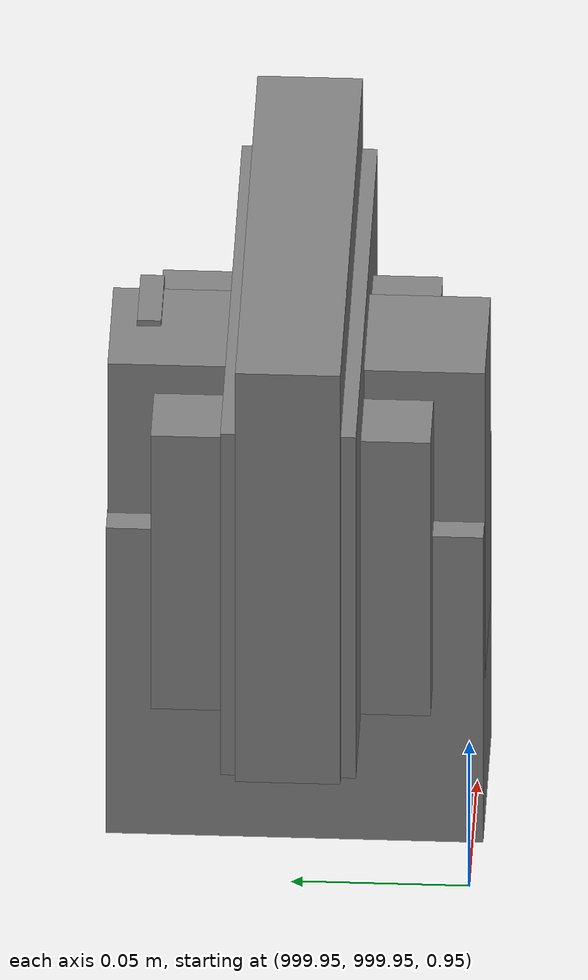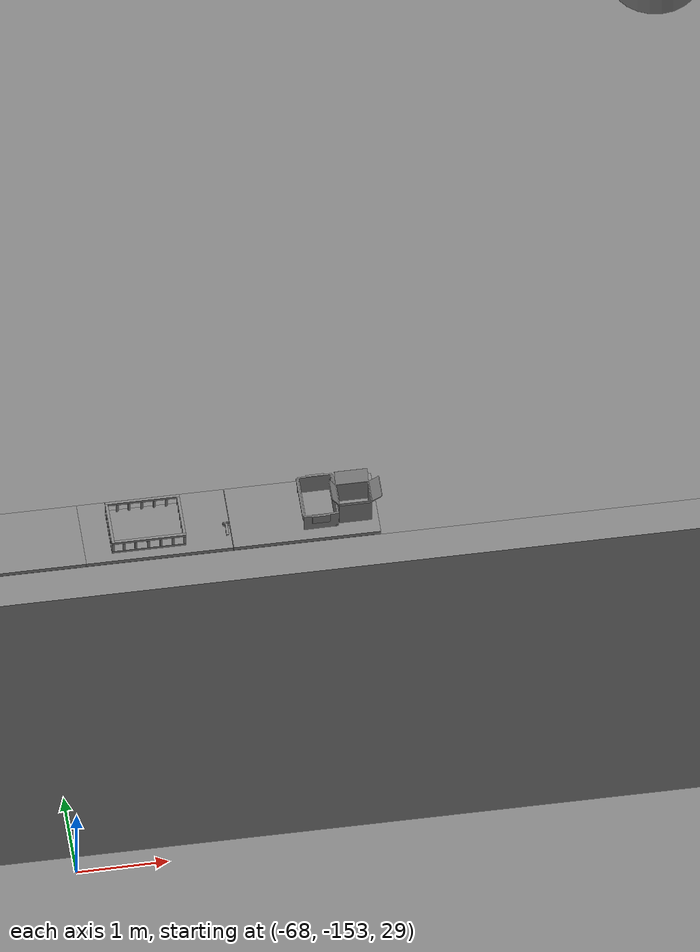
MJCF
<mujoco>
    <option gravity="0.000000000 0.000000000 -9.810000420" timestep="0.0049999999" integrator="implicitfast" density="1.225" viscosity="1.8000001e-05" noslip_iterations="10" iterations="100" sdf_iterations="50">
        <flag multiccd="disable"/>
    </option>
    <size memory="1000M"/>
    <compiler coordinate="local"/>
    <worldbody>
        <light cutoff="30" pos="0 1 1" dir="0 -1 -2"/>
        <light cutoff="30" pos="0 -1 1" dir="0 1 -2"/>
        <body pos="-66.027214050 -149.048370361 31.165897369" euler="136.259429932 37.065120697 -107.212326050" mocap="true" name="spotlight4_SpotLight"/>
        <body pos="1000.000000000 1000.000000000 1.000000000" euler="0.000000000 0.000000000 180.000000000" name="openloong_gripper_2f85_fix_base_usda_battery_01">
            <geom contype="1" conaffinity="1" density="1000" type="box" material="" rgba="0.500000000 0.500000000 0.500000000 1.000000000" solimp="0.899999976 0.949999988 0.001000000" friction="1.000000000 0.005000000 0.000100000" solref="0.020000000 1.000000000" margin="0" condim="3" group="0" pos="-0.011123657 -0.041940309 0.101691343" quat="1.000000000 0.000000000 0.000000000 0.000000000" size="0.010800000 0.003375000 0.004725000" name="openloong_gripper_2f85_fix_base_usda_geom_4AF07345_FE58_4B34_8894_FC267EE04B27"/>
            <geom contype="1" conaffinity="1" density="1000" type="box" material="" rgba="0.500000000 0.500000000 0.500000000 1.000000000" solimp="0.899999976 0.949999988 0.001000000" friction="1.000000000 0.005000000 0.000100000" solref="0.020000000 1.000000000" margin="0" condim="3" group="0" pos="-0.010876465 -0.044247437 0.047066893" quat="0.998702705 -0.050920475 0.000000000 0.000000000" size="0.009450001 0.002700000 0.024975000" name="openloong_gripper_2f85_fix_base_usda_geom_21E74614_B113_4EBA_8585_6D1A2D74E49C"/>
            <geom contype="1" conaffinity="1" density="1000" type="box" material="" rgba="0.500000000 0.500000000 0.500000000 1.000000000" solimp="0.899999976 0.949999988 0.001000000" friction="1.000000000 0.005000000 0.000100000" solref="0.020000000 1.000000000" margin="0" condim="3" group="0" pos="-0.001235962 -0.000659180 0.047381196" quat="1.000000000 0.000000000 0.000000000 0.000000000" size="0.039420001 0.039150000 0.047250003" name="openloong_gripper_2f85_fix_base_usda_geom_B0EE4D49_47EF_4AD3_87CB_9DA7BF510F2A"/>
            <geom contype="1" conaffinity="1" density="1000" type="box" material="" rgba="0.500000000 0.500000000 0.500000000 1.000000000" solimp="0.899999976 0.949999988 0.001000000" friction="1.000000000 0.005000000 0.000100000" solref="0.020000000 1.000000000" margin="0" condim="3" group="0" pos="-0.010876465 -0.039138794 0.009851727" quat="1.000000000 0.000000000 0.000000000 0.000000000" size="0.009450001 0.010800000 0.013500000" name="openloong_gripper_2f85_fix_base_usda_geom_F26976BA_CB97_4FE9_8190_729AB6F053A6"/>
            <geom contype="1" conaffinity="1" density="1000" type="box" material="" rgba="0.500000000 0.500000000 0.500000000 1.000000000" solimp="0.899999976 0.949999988 0.001000000" friction="1.000000000 0.005000000 0.000100000" solref="0.020000000 1.000000000" margin="0" condim="3" group="0" pos="-0.010876465 -0.041528322 0.071508206" quat="1.000000000 0.000000000 0.000000000 0.000000000" size="0.009450001 0.002700000 0.027000001" name="openloong_gripper_2f85_fix_base_usda_geom_ADC7824A_8DBA_4A9A_B138_86EF46081151"/>
            <freejoint name="openloong_gripper_2f85_fix_base_usda_battery_01_joint"/>
            <site size="0.005000000 0.005000000 0.005000000" rgba="0.500000000 0.500000000 0.500000000 1.000000000" pos="0.000000000 0.000000000 0.000000000" quat="0.999961913 0.008726500 0.000000000 0.000000000" group="0" type="sphere" name="openloong_gripper_2f85_fix_base_usda_battery_01site"/>
        </body>
        <body pos="-65.877983093 -149.624526978 31.171112061" euler="99.564453125 -31.437179565 -114.035148621" mocap="true" name="spotlight3_SpotLight"/>
        <body pos="1000.000000000 1000.000000000 1.000000000" euler="0.000000000 0.000000000 180.000000000" name="openloong_gripper_2f85_fix_base_usda_cpu_fan">
            <geom contype="1" conaffinity="1" density="1000" type="box" material="" rgba="0.500000000 0.500000000 0.500000000 1.000000000" solimp="0.899999976 0.949999988 0.001000000" friction="1.000000000 0.005000000 0.000100000" solref="0.020000000 1.000000000" margin="0" condim="3" group="0" pos="0.000000000 0.000000000 0.070034981" quat="0.000000000 0.000000000 0.000000000 1.000000000" size="0.070700005 0.014699999 0.070700005" name="openloong_gripper_2f85_fix_base_usda_geom_EDA5EB3A_D3D1_48E7_A46B_AFC5BDA93CFA"/>
            <freejoint name="openloong_gripper_2f85_fix_base_usda_cpu_fan_joint"/>
            <site size="0.005000000 0.005000000 0.005000000" rgba="0.500000000 0.500000000 0.500000000 1.000000000" pos="0.000000000 0.000000000 0.000000000" quat="0.999961913 0.008726535 0.000000000 0.000000000" group="0" type="sphere" name="openloong_gripper_2f85_fix_base_usda_cpu_fancsite"/>
        </body>
        <body pos="1000.000000000 1000.000000000 1.000000000" euler="0.000000000 0.000000000 180.000000000" name="openloong_gripper_2f85_fix_base_usda_wifi_box">
            <geom contype="1" conaffinity="1" density="1000" type="box" material="" rgba="0.500000000 0.500000000 0.500000000 1.000000000" solimp="0.899999976 0.949999988 0.001000000" friction="1.000000000 0.005000000 0.000100000" solref="0.020000000 1.000000000" margin="0" condim="3" group="0" pos="0.000000000 0.000000000 0.058978677" quat="0.000000000 0.000000047 0.000000000 1.000000000" size="0.068499997 0.018999999 0.059000000" name="openloong_gripper_2f85_fix_base_usda_geom_A2CBCA88_D13D_4B83_AE20_6A5409C3F855"/>
            <freejoint name="openloong_gripper_2f85_fix_base_usda_wifi_box_joint"/>
            <site size="0.005000000 0.005000000 0.005000000" rgba="0.500000000 0.500000000 0.500000000 1.000000000" pos="0.000000000 0.000000000 0.000000000" quat="0.999961913 0.008726500 0.000000000 0.000000000" group="0" type="sphere" name="openloong_gripper_2f85_fix_base_usda_wifi_boxsite"/>
        </body>
        <body pos="1000.000000000 1000.000000000 1.000000000" euler="0.000011953 0.000005123 -179.999984741" name="openloong_gripper_2f85_fix_base_usda_intel_box">
            <geom contype="1" conaffinity="1" density="1000" type="box" material="" rgba="0.500000000 0.500000000 0.500000000 1.000000000" solimp="0.899999976 0.949999988 0.001000000" friction="1.000000000 0.005000000 0.000100000" solref="0.020000000 1.000000000" margin="0" condim="3" group="0" pos="0.000000000 -0.000067139 0.000082284" quat="0.707106709 0.000000225 0.000000253 0.707106650" size="0.052800003 0.025300000 0.052800003" name="openloong_gripper_2f85_fix_base_usda_geom_530823C8_2CE1_4880_9F40_A81135910190"/>
            <freejoint name="openloong_gripper_2f85_fix_base_usda_intel_box_joint"/>
            <site size="0.005000000 0.005000000 0.005000000" rgba="0.500000000 0.500000000 0.500000000 1.000000000" pos="0.000000000 0.000000000 0.000000000" quat="0.999961913 0.008726500 0.000000000 0.000000000" group="0" type="sphere" name="openloong_gripper_2f85_fix_base_usda_intel_boxsite"/>
        </body>
        <body pos="-65.866996765 -149.623596191 31.166255951" euler="-51.205505371 -25.604440689 75.422470093" mocap="true" name="spotlight5_SpotLight"/>
        <body pos="1000.000000000 999.999938965 1.000000000" euler="0.000000000 0.000000000 180.000000000" name="openloong_gripper_2f85_fix_base_usda_intelcore_i5">
            <geom contype="1" conaffinity="1" density="1000" type="box" material="" rgba="0.500000000 0.500000000 0.500000000 1.000000000" solimp="0.899999976 0.949999988 0.001000000" friction="1.000000000 0.005000000 0.000100000" solref="0.020000000 1.000000000" margin="0" condim="3" group="0" pos="0.000000000 0.000000000 0.051722717" quat="0.707106709 0.000000000 0.000000000 -0.707106769" size="0.052800000 0.018080002 0.052800000" name="openloong_gripper_2f85_fix_base_usda_geom_BD70AC0C_5DC8_4F04_B555_586BCFC0B7F0"/>
            <freejoint name="openloong_gripper_2f85_fix_base_usda_intelcore_i5_joint"/>
            <site size="0.005000000 0.005000000 0.005000000" rgba="0.500000000 0.500000000 0.500000000 1.000000000" pos="0.000000000 0.000000000 0.000000000" quat="0.999961913 0.008726534 0.000000000 0.000000000" group="0" type="sphere" name="openloong_gripper_2f85_fix_base_usda_intelcore_i5site"/>
        </body>
        <body pos="-64.866622925 -149.383972168 30.183746338" euler="89.999984741 89.999946594 0.000000000" name="openloong_gripper_2f85_fix_base_usda_bluebox_01">
            <geom contype="1" conaffinity="1" density="1000" type="box" material="" rgba="0.500000000 0.500000000 0.500000000 1.000000000" solimp="0.899999976 0.949999988 0.001000000" friction="1.000000000 0.005000000 0.000100000" solref="0.020000000 1.000000000" margin="0" condim="3" group="0" pos="0.276580811 0.187225342 0.000068665" quat="0.707106948 0.000077471 0.707106352 0.000077486" size="0.100000001 0.057999998 0.010000000" name="openloong_gripper_2f85_fix_base_usda_geom_3AC4F622_491E_4266_BAC1_3F666890E540"/>
            <geom contype="1" conaffinity="1" density="1000" type="box" material="" rgba="0.500000000 0.500000000 0.500000000 1.000000000" solimp="0.899999976 0.949999988 0.001000000" friction="1.000000000 0.005000000 0.000100000" solref="0.020000000 1.000000000" margin="0" condim="3" group="0" pos="0.000000000 0.002883911 0.000000000" quat="0.999999881 0.000000000 0.000000000 0.000000000" size="0.254000008 0.003000000 0.172000006" name="openloong_gripper_2f85_fix_base_usda_geom_D5C06BD5_6921_40A0_877A_894F840C0ECF"/>
            <geom contype="1" conaffinity="1" density="1000" type="box" material="" rgba="0.500000000 0.500000000 0.500000000 1.000000000" solimp="0.899999976 0.949999988 0.001000000" friction="1.000000000 0.005000000 0.000100000" solref="0.020000000 1.000000000" margin="0" condim="3" group="0" pos="0.000000000 0.124874115 0.173484802" quat="0.999796331 0.020176515 -0.000000015 0.000000030" size="0.259999990 0.119999997 0.007000000" name="openloong_gripper_2f85_fix_base_usda_geom_C2D809C3_3418_49A2_9DAB_2CECBA10D1F1"/>
            <geom contype="1" conaffinity="1" density="1000" type="box" material="" rgba="0.500000000 0.500000000 0.500000000 1.000000000" solimp="0.899999976 0.949999988 0.001000000" friction="1.000000000 0.005000000 0.000100000" solref="0.020000000 1.000000000" margin="0" condim="3" group="0" pos="0.000000000 0.124874115 -0.173469543" quat="0.999796331 -0.020176545 -0.000000015 0.000000000" size="0.259999990 0.119999997 0.007000000" name="openloong_gripper_2f85_fix_base_usda_geom_EDBF0D41_2740_4A1C_BCE2_0590858EBECD"/>
            <geom contype="1" conaffinity="1" density="1000" type="box" material="" rgba="0.500000000 0.500000000 0.500000000 1.000000000" solimp="0.899999976 0.949999988 0.001000000" friction="1.000000000 0.005000000 0.000100000" solref="0.020000000 1.000000000" margin="0" condim="3" group="0" pos="0.000000000 0.214008331 0.188980103" quat="0.999912977 0.013176724 0.000000015 0.000000000" size="0.259999990 0.029999999 0.012500000" name="openloong_gripper_2f85_fix_base_usda_geom_0CBB69ED_37B7_48FA_811F_3F8A1B982FAF"/>
            <geom contype="1" conaffinity="1" density="1000" type="box" material="" rgba="0.500000000 0.500000000 0.500000000 1.000000000" solimp="0.899999976 0.949999988 0.001000000" friction="1.000000000 0.005000000 0.000100000" solref="0.020000000 1.000000000" margin="0" condim="3" group="0" pos="-0.258361816 0.125289917 0.001876831" quat="0.702796936 -0.020792112 0.710783124 0.020769298" size="0.189999998 0.119999997 0.009000000" name="openloong_gripper_2f85_fix_base_usda_geom_95D3552B_0B6E_4EA2_9D75_8C3D33A30AD2"/>
            <geom contype="1" conaffinity="1" density="1000" type="box" material="" rgba="0.500000000 0.500000000 0.500000000 1.000000000" solimp="0.899999976 0.949999988 0.001000000" friction="1.000000000 0.005000000 0.000100000" solref="0.020000000 1.000000000" margin="0" condim="3" group="0" pos="0.000000000 0.214008331 -0.188980103" quat="0.999912977 -0.013176769 0.000000030 0.000000015" size="0.259999990 0.029999999 0.012500000" name="openloong_gripper_2f85_fix_base_usda_geom_7120BBC1_5146_4CC1_B8E4_047647CE1F00"/>
            <geom contype="1" conaffinity="1" density="1000" type="box" material="" rgba="0.500000000 0.500000000 0.500000000 1.000000000" solimp="0.899999976 0.949999988 0.001000000" friction="1.000000000 0.005000000 0.000100000" solref="0.020000000 1.000000000" margin="0" condim="3" group="0" pos="-0.276611328 0.187225342 0.000068665" quat="0.707106650 0.000077441 0.707106709 0.000077456" size="0.100000001 0.057999998 0.010000000" name="openloong_gripper_2f85_fix_base_usda_geom_AE2C6F03_C308_40EA_A367_58E4C5754294"/>
            <geom contype="1" conaffinity="1" density="1000" type="box" material="" rgba="0.500000000 0.500000000 0.500000000 1.000000000" solimp="0.899999976 0.949999988 0.001000000" friction="1.000000000 0.005000000 0.000100000" solref="0.020000000 1.000000000" margin="0" condim="3" group="0" pos="0.258331299 0.125289917 0.001876831" quat="0.702851415 0.018856421 0.710823774 -0.019329369" size="0.189999998 0.119999997 0.009000000" name="openloong_gripper_2f85_fix_base_usda_geom_EE568AD6_8588_4DC0_A9AD_A8EABA2E0385"/>
            <freejoint name="openloong_gripper_2f85_fix_base_usda_bluebox_01_joint"/>
            <site size="0.005000000 0.005000000 0.005000000" rgba="0.500000000 0.500000000 0.500000000 1.000000000" pos="0.000000000 0.000000000 0.000000000" quat="0.999961913 0.008726534 0.000000000 0.000000000" group="0" type="sphere" name="openloong_gripper_2f85_fix_base_usda_bluebox_01site"/>
        </body>
        <body pos="-64.496299744 -149.491867065 30.235729218" euler="0.000000000 0.000000000 89.999946594" name="openloong_gripper_2f85_fix_base_usda_cardboardbox_01">
            <geom contype="1" conaffinity="1" density="1000" type="box" material="" rgba="0.500000000 0.500000000 0.500000000 1.000000000" solimp="0.899999976 0.949999988 0.001000000" friction="1.000000000 0.005000000 0.000100000" solref="0.020000000 1.000000000" margin="0" condim="3" group="0" pos="-0.003166199 -0.004086494 0.005052090" quat="1.000000000 0.000000000 0.000000000 0.000000000" size="0.142499998 0.177500010 0.005000000" name="openloong_gripper_2f85_fix_base_usda_geom_BEA39102_BB88_498D_A6E4_BDF3D884EACB"/>
            <geom contype="1" conaffinity="1" density="1000" type="box" material="" rgba="0.500000000 0.500000000 0.500000000 1.000000000" solimp="0.899999976 0.949999988 0.001000000" friction="1.000000000 0.005000000 0.000100000" solref="0.020000000 1.000000000" margin="0" condim="3" group="0" pos="-0.003166199 0.170316696 0.150570869" quat="1.000000000 0.000000000 0.000000000 0.000000000" size="0.142499998 0.005000000 0.149999991" name="openloong_gripper_2f85_fix_base_usda_geom_6DB1005F_3362_4EA9_B549_9CA8953478E2"/>
            <geom contype="1" conaffinity="1" density="1000" type="box" material="" rgba="0.500000000 0.500000000 0.500000000 1.000000000" solimp="0.899999976 0.949999988 0.001000000" friction="1.000000000 0.005000000 0.000100000" solref="0.020000000 1.000000000" margin="0" condim="3" group="0" pos="-0.147399902 -0.005307198 0.150570869" quat="1.000000000 0.000000000 0.000000000 0.000000000" size="0.005000000 0.177500010 0.149999991" name="openloong_gripper_2f85_fix_base_usda_geom_A831C686_DA49_4AE8_9BCC_1874053773E7"/>
            <geom contype="1" conaffinity="1" density="1000" type="box" material="" rgba="0.500000000 0.500000000 0.500000000 1.000000000" solimp="0.899999976 0.949999988 0.001000000" friction="1.000000000 0.005000000 0.000100000" solref="0.020000000 1.000000000" margin="0" condim="3" group="0" pos="0.140275955 -0.005307198 0.150570869" quat="1.000000000 0.000000000 0.000000000 0.000000000" size="0.005000000 0.177500010 0.149999991" name="openloong_gripper_2f85_fix_base_usda_geom_3B5144E0_4F02_449A_AE46_DBE57B3F86AD"/>
            <geom contype="1" conaffinity="1" density="1000" type="box" material="" rgba="0.500000000 0.500000000 0.500000000 1.000000000" solimp="0.899999976 0.949999988 0.001000000" friction="1.000000000 0.005000000 0.000100000" solref="0.020000000 1.000000000" margin="0" condim="3" group="0" pos="-0.003166199 -0.181550980 0.150570869" quat="1.000000000 0.000000000 0.000000000 0.000000000" size="0.142499998 0.005000000 0.149999991" name="openloong_gripper_2f85_fix_base_usda_geom_1E99EB39_09E3_4581_AC40_14B38F65AA92"/>
            <freejoint name="openloong_gripper_2f85_fix_base_usda_cardboardbox_01_joint"/>
            <site size="0.005000000 0.005000000 0.005000000" rgba="0.500000000 0.500000000 0.500000000 1.000000000" pos="0.000000000 0.000000000 0.000000000" quat="0.999961913 0.008726535 0.000000000 0.000000000" group="0" type="sphere" name="openloong_gripper_2f85_fix_base_usda_site_B440A28E_7268_4E07_90A3_95846EDDC65D"/>
            <body pos="0.139160156 -0.004048347 0.301930904" euler="-179.999954224 49.383502960 179.999954224" name="openloong_gripper_2f85_fix_base_usda_A1_006">
                <geom contype="1" conaffinity="1" density="1000" type="box" material="" rgba="0.500000000 0.500000000 0.500000000 1.000000000" solimp="0.899999976 0.949999988 0.001000000" friction="1.000000000 0.005000000 0.000100000" solref="0.020000000 1.000000000" margin="0" condim="3" group="0" pos="-0.071587563 0.000009537 0.001745224" quat="0.999999881 0.000000000 0.000000000 0.000000000" size="0.071249999 0.179999992 0.002500000" name="openloong_gripper_2f85_fix_base_usda_geom_1F3B1A72_0D04_4A3E_A51F_8EFB9E6C704D"/>
                <joint armature="0" stiffness="0.07" damping="0.0099999998" axis="0.000000 1.000000 0.000000" type="hinge" name="openloong_gripper_2f85_fix_base_usda_A1_006"/>
            </body>
            <body pos="-0.145902634 -0.004086494 0.301938057" euler="-180.000000000 -60.000011444 -180.000000000" name="openloong_gripper_2f85_fix_base_usda_A2_006">
                <geom contype="1" conaffinity="1" density="1000" type="box" material="" rgba="0.500000000 0.500000000 0.500000000 1.000000000" solimp="0.899999976 0.949999988 0.001000000" friction="1.000000000 0.005000000 0.000100000" solref="0.020000000 1.000000000" margin="0" condim="3" group="0" pos="0.071268082 0.000009537 0.002717972" quat="0.000002921 0.000000000 -0.000000030 0.999999881" size="0.071249999 0.179999992 0.002500000" name="openloong_gripper_2f85_fix_base_usda_geom_A61A56D1_8E73_4384_8D21_F847CA2D9F38"/>
                <joint armature="0" stiffness="0.07" damping="0.0099999998" axis="0.000000 1.000000 0.000000" type="hinge" name="openloong_gripper_2f85_fix_base_usda_A2_006"/>
            </body>
            <body pos="-0.003385544 0.175991058 0.301930904" euler="-125.858116150 -0.000004561 0.000002331" name="openloong_gripper_2f85_fix_base_usda_B2_006">
                <geom contype="1" conaffinity="1" density="1000" type="box" material="" rgba="0.500000000 0.500000000 0.500000000 1.000000000" solimp="0.899999976 0.949999988 0.001000000" friction="1.000000000 0.005000000 0.000100000" solref="0.020000000 1.000000000" margin="0" condim="3" group="0" pos="0.000009537 -0.070939064 -0.002470016" quat="0.999614120 0.027776197 -0.000000015 0.000000030" size="0.137500003 0.064999998 0.005000000" name="openloong_gripper_2f85_fix_base_usda_geom_781F02B3_11D0_4DB0_888D_168F17DA57E7"/>
                <joint armature="0" stiffness="0.07" damping="0.0099999998" axis="1.000000 0.000000 0.000000" type="hinge" name="openloong_gripper_2f85_fix_base_usda_B2_006"/>
            </body>
            <body pos="-0.003385544 -0.184140205 0.301938057" euler="147.805557251 0.000000000 0.000000000" name="openloong_gripper_2f85_fix_base_usda_B1_006">
                <geom contype="1" conaffinity="1" density="1000" type="box" material="" rgba="0.500000000 0.500000000 0.500000000 1.000000000" solimp="0.899999976 0.949999988 0.001000000" friction="1.000000000 0.005000000 0.000100000" solref="0.020000000 1.000000000" margin="0" condim="3" group="0" pos="-0.000028610 0.070202351 -0.002703667" quat="0.999614179 -0.027776167 0.000000000 0.000000000" size="0.137500003 0.064999998 0.005000000" name="openloong_gripper_2f85_fix_base_usda_geom_3179A38C_6087_49EF_84A3_8B9011F8219E"/>
                <joint armature="0" stiffness="0.07" damping="0.0099999998" axis="1.000000 0.000000 0.000000" type="hinge" name="openloong_gripper_2f85_fix_base_usda_B1_006"/>
            </body>
        </body>
        <body pos="-65.882858276 -149.481979370 30.229999542" euler="-64.487716675 0.000000000 0.000000000" name="openloong_gripper_2f85_fix_base_usda_Barcode">
            <geom contype="1" conaffinity="1" density="1000" type="box" material="" rgba="0.500000000 0.500000000 0.500000000 1.000000000" solimp="0.899999976 0.949999988 0.001000000" friction="1.000000000 0.005000000 0.000100000" solref="0.020000000 1.000000000" margin="0" condim="3" group="0" pos="0.000000000 0.013038635 0.001419067" quat="0.000000000 0.000000000 0.000000000 1.000000119" size="0.034000002 0.010000000 0.017999999" name="openloong_gripper_2f85_fix_base_usda_geom_8153C939_5EB6_4409_9C21_2DC82B877565"/>
            <geom contype="1" conaffinity="1" density="1000" type="box" material="" rgba="0.500000000 0.500000000 0.500000000 1.000000000" solimp="0.899999976 0.949999988 0.001000000" friction="1.000000000 0.005000000 0.000100000" solref="0.020000000 1.000000000" margin="0" condim="3" group="0" pos="0.000000000 -0.035301208 -0.007095337" quat="0.000000000 0.000000000 -0.043619365 0.999048233" size="0.028999999 0.010000000 0.020000000" name="openloong_gripper_2f85_fix_base_usda_geom_F8AF3E3F_8972_4D98_8202_C178B79CA54A"/>
            <geom contype="1" conaffinity="1" density="1000" type="box" material="" rgba="0.500000000 0.500000000 0.500000000 1.000000000" solimp="0.899999976 0.949999988 0.001000000" friction="1.000000000 0.005000000 0.000100000" solref="0.020000000 1.000000000" margin="0" condim="3" group="0" pos="0.000000000 -0.043411255 -0.011749268" quat="0.922262907 0.386563420 0.000000000 0.000000000" size="0.026000001 0.010000000 0.020000000" name="openloong_gripper_2f85_fix_base_usda_geom_BC919F6A_315D_4623_B500_82B5D46E1A9C"/>
            <geom contype="1" conaffinity="1" density="1000" type="box" material="" rgba="0.500000000 0.500000000 0.500000000 1.000000000" solimp="0.899999976 0.949999988 0.001000000" friction="1.000000000 0.005000000 0.000100000" solref="0.020000000 1.000000000" margin="0" condim="3" group="0" pos="0.000000000 -0.016967773 -0.031860352" quat="0.000000000 0.000000000 0.000000000 1.000000119" size="0.008000000 0.010000000 0.013000000" name="openloong_gripper_2f85_fix_base_usda_geom_FA405FED_1B07_480D_AC6E_D613D7FD6D98"/>
            <geom contype="1" conaffinity="1" density="1000" type="box" material="" rgba="0.500000000 0.500000000 0.500000000 1.000000000" solimp="0.899999976 0.949999988 0.001000000" friction="1.000000000 0.005000000 0.000100000" solref="0.020000000 1.000000000" margin="0" condim="3" group="0" pos="0.000000000 -0.001869202 0.000312805" quat="0.953716993 0.300705761 0.000000000 0.000000000" size="0.032000002 0.010000000 0.018999999" name="openloong_gripper_2f85_fix_base_usda_geom_84762408_5436_4A98_8382_3782E24EC669"/>
            <geom contype="1" conaffinity="1" density="1000" type="box" material="" rgba="0.500000000 0.500000000 0.500000000 1.000000000" solimp="0.899999976 0.949999988 0.001000000" friction="1.000000000 0.005000000 0.000100000" solref="0.020000000 1.000000000" margin="0" condim="3" group="0" pos="0.000000000 -0.019531250 -0.003173828" quat="0.953716993 0.300705761 0.000000000 0.000000000" size="0.030999999 0.010000000 0.020000000" name="openloong_gripper_2f85_fix_base_usda_geom_FC714940_DDA9_4079_A53C_2D9F31C4CEE9"/>
            <geom contype="1" conaffinity="1" density="1000" type="box" material="" rgba="0.500000000 0.500000000 0.500000000 1.000000000" solimp="0.899999976 0.949999988 0.001000000" friction="1.000000000 0.005000000 0.000100000" solref="0.020000000 1.000000000" margin="0" condim="3" group="0" pos="0.000000000 -0.035301208 -0.007095337" quat="0.953716993 0.300705761 0.000000000 0.000000000" size="0.028999999 0.010000000 0.020000000" name="openloong_gripper_2f85_fix_base_usda_geom_3ED418B4_959F_4DA4_AE2C_9B4797E0EF23"/>
            <geom contype="1" conaffinity="1" density="1000" type="box" material="" rgba="0.500000000 0.500000000 0.500000000 1.000000000" solimp="0.899999976 0.949999988 0.001000000" friction="1.000000000 0.005000000 0.000100000" solref="0.020000000 1.000000000" margin="0" condim="3" group="0" pos="0.000000000 -0.042617798 -0.071121216" quat="0.000000000 0.000000000 0.000000000 1.000000119" size="0.013000000 0.021000000 0.059999999" name="openloong_gripper_2f85_fix_base_usda_geom_596E8E63_FED0_44B4_80A1_7801B2DE40F1"/>
            <freejoint name="openloong_gripper_2f85_fix_base_usda_Barcode_joint"/>
            <site size="0.005000000 0.005000000 0.005000000" rgba="0.500000000 0.500000000 0.500000000 1.000000000" pos="0.000000000 0.000000000 0.000000000" quat="1.000000000 0.000000000 0.000000000 0.000000000" group="0" type="sphere" name="openloong_gripper_2f85_fix_base_usda_Barcode_site"/>
        </body>
        <body pos="-66.745018005 -149.392349243 30.184000015" euler="0.000000000 0.000000000 89.999946594" name="[22330384516284]_Basket_01">
            <geom contype="1" conaffinity="1" density="1000" type="box" material="" rgba="0.500000000 0.500000000 0.500000000 1.000000000" solimp="0.899999976 0.949999988 0.001000000" friction="1.000000000 0.005000000 0.000100000" solref="0.020000000 1.000000000" margin="0" condim="3" group="0" pos="-0.052425385 0.389207840 0.089787483" quat="0.707107008 0.000000000 0.000000000 0.707106411" size="0.014249999 0.014249999 0.059999999" name="[22330384516284]_geom_1F036DC1_7EA3_42F5_A878_2F577FB23B36"/>
            <geom contype="1" conaffinity="1" density="1000" type="box" material="" rgba="0.500000000 0.500000000 0.500000000 1.000000000" solimp="0.899999976 0.949999988 0.001000000" friction="1.000000000 0.005000000 0.000100000" solref="0.020000000 1.000000000" margin="0" condim="3" group="0" pos="0.264015198 -0.133043289 0.089787483" quat="0.707107008 0.000000000 0.000000000 0.707106411" size="0.014249999 0.014249999 0.059999999" name="[22330384516284]_geom_38E08AE4_5E60_48DE_92B5_78AA4CB60E52"/>
            <geom contype="1" conaffinity="1" density="1000" type="box" material="" rgba="0.500000000 0.500000000 0.500000000 1.000000000" solimp="0.899999976 0.949999988 0.001000000" friction="1.000000000 0.005000000 0.000100000" solref="0.020000000 1.000000000" margin="0" condim="3" group="0" pos="-0.264015198 -0.265548706 0.089793205" quat="0.707107008 0.000000000 0.000000000 0.707106411" size="0.014249999 0.014249999 0.059999999" name="[22330384516284]_geom_093109CC_C53B_455C_BBE7_7E710A75C5A9"/>
            <geom contype="1" conaffinity="1" density="1000" type="box" material="" rgba="0.500000000 0.500000000 0.500000000 1.000000000" solimp="0.899999976 0.949999988 0.001000000" friction="1.000000000 0.005000000 0.000100000" solref="0.020000000 1.000000000" margin="0" condim="3" group="0" pos="-0.160263062 -0.389322281 0.089793205" quat="0.707107008 0.000000000 0.000000000 0.707106411" size="0.014249999 0.014249999 0.059999999" name="[22330384516284]_geom_1AD883D5_9BD7_420E_B3C0_24151489DE44"/>
            <geom contype="1" conaffinity="1" density="1000" type="box" material="" rgba="0.500000000 0.500000000 0.500000000 1.000000000" solimp="0.899999976 0.949999988 0.001000000" friction="1.000000000 0.005000000 0.000100000" solref="0.020000000 1.000000000" margin="0" condim="3" group="0" pos="0.162265778 -0.389322281 0.089787483" quat="0.707107008 0.000000000 0.000000000 0.707106411" size="0.014249999 0.014249999 0.059999999" name="[22330384516284]_geom_DAA4A2EF_F079_424D_96F8_1EE3EC1BEA85"/>
            <geom contype="1" conaffinity="1" density="1000" type="box" material="" rgba="0.500000000 0.500000000 0.500000000 1.000000000" solimp="0.899999976 0.949999988 0.001000000" friction="1.000000000 0.005000000 0.000100000" solref="0.020000000 1.000000000" margin="0" condim="3" group="0" pos="0.264015198 0.389207840 0.089787483" quat="0.707107008 0.000000000 0.000000000 0.707106411" size="0.014249999 0.014249999 0.059999999" name="[22330384516284]_geom_34F090F3_B439_4D8F_ABD0_851AD7E4D26C"/>
            <geom contype="1" conaffinity="1" density="1000" type="box" material="" rgba="0.500000000 0.500000000 0.500000000 1.000000000" solimp="0.899999976 0.949999988 0.001000000" friction="1.000000000 0.005000000 0.000100000" solref="0.020000000 1.000000000" margin="0" condim="3" group="0" pos="-0.264015198 -0.133043289 0.089793205" quat="0.707107008 0.000000000 0.000000000 0.707106411" size="0.014249999 0.014249999 0.059999999" name="[22330384516284]_geom_2C213DDF_178D_4748_9B55_9DB3DD361B96"/>
            <geom contype="1" conaffinity="1" density="1000" type="box" material="" rgba="0.500000000 0.500000000 0.500000000 1.000000000" solimp="0.899999976 0.949999988 0.001000000" friction="1.000000000 0.005000000 0.000100000" solref="0.020000000 1.000000000" margin="0" condim="3" group="0" pos="-0.264026642 0.269256592 0.089793205" quat="0.707107008 0.000000000 0.000000000 0.707106411" size="0.014249999 0.014249999 0.059999999" name="[22330384516284]_geom_9D8AD0DA_2F1B_46F2_A37E_C5AFA7D9DB73"/>
            <geom contype="1" conaffinity="1" density="1000" type="box" material="" rgba="0.500000000 0.500000000 0.500000000 1.000000000" solimp="0.899999976 0.949999988 0.001000000" friction="1.000000000 0.005000000 0.000100000" solref="0.020000000 1.000000000" margin="0" condim="3" group="0" pos="0.054462433 0.389207840 0.089787483" quat="0.707107008 0.000000000 0.000000000 0.707106411" size="0.014249999 0.014249999 0.059999999" name="[22330384516284]_geom_8E4F5B8C_7712_499A_B3B9_81E87286A5D8"/>
            <geom contype="1" conaffinity="1" density="1000" type="box" material="" rgba="0.500000000 0.500000000 0.500000000 1.000000000" solimp="0.899999976 0.949999988 0.001000000" friction="1.000000000 0.005000000 0.000100000" solref="0.020000000 1.000000000" margin="0" condim="3" group="0" pos="0.054462433 -0.389322281 0.089787483" quat="0.707107008 0.000000000 0.000000000 0.707106411" size="0.014249999 0.014249999 0.059999999" name="[22330384516284]_geom_4822CAD0_BCE6_4928_B7CD_CE783120F024"/>
            <geom contype="1" conaffinity="1" density="1000" type="box" material="" rgba="0.500000000 0.500000000 0.500000000 1.000000000" solimp="0.899999976 0.949999988 0.001000000" friction="1.000000000 0.005000000 0.000100000" solref="0.020000000 1.000000000" margin="0" condim="3" group="0" pos="0.264015198 0.269256592 0.089793205" quat="0.707107008 0.000000000 0.000000000 0.707106411" size="0.014249999 0.014249999 0.059999999" name="[22330384516284]_geom_DCAECA28_5367_40D7_B346_E80B4B2E3FEB"/>
            <geom contype="1" conaffinity="1" density="1000" type="box" material="" rgba="0.500000000 0.500000000 0.500000000 1.000000000" solimp="0.899999976 0.949999988 0.001000000" friction="1.000000000 0.005000000 0.000100000" solref="0.020000000 1.000000000" margin="0" condim="3" group="0" pos="0.264015198 -0.389322281 0.089787483" quat="0.707107008 0.000000000 0.000000000 0.707106411" size="0.014249999 0.014249999 0.059999999" name="[22330384516284]_geom_9610806D_7ACC_4E10_A741_55391356FB14"/>
            <geom contype="1" conaffinity="1" density="1000" type="box" material="" rgba="0.500000000 0.500000000 0.500000000 1.000000000" solimp="0.899999976 0.949999988 0.001000000" friction="1.000000000 0.005000000 0.000100000" solref="0.020000000 1.000000000" margin="0" condim="3" group="0" pos="0.000000000 0.000000000 0.015998840" quat="0.707107008 0.000000000 0.000000000 0.707106411" size="0.403499991 0.279000014 0.015750000" name="[22330384516284]_geom_28F25320_9E92_45D8_85D5_2F3827DFDFDC"/>
            <geom contype="1" conaffinity="1" density="1000" type="box" material="" rgba="0.500000000 0.500000000 0.500000000 1.000000000" solimp="0.899999976 0.949999988 0.001000000" friction="1.000000000 0.005000000 0.000100000" solref="0.020000000 1.000000000" margin="0" condim="3" group="0" pos="0.000000000 -0.389476776 0.163619041" quat="0.707107008 0.000000000 0.000000000 0.707106411" size="0.015000000 0.277500004 0.015750000" name="[22330384516284]_geom_E4E7C717_B750_456C_AF2B_427CA1DE5157"/>
            <geom contype="1" conaffinity="1" density="1000" type="box" material="" rgba="0.500000000 0.500000000 0.500000000 1.000000000" solimp="0.899999976 0.949999988 0.001000000" friction="1.000000000 0.005000000 0.000100000" solref="0.020000000 1.000000000" margin="0" condim="3" group="0" pos="0.162265778 0.389207840 0.089787483" quat="0.707107008 0.000000000 0.000000000 0.707106411" size="0.014249999 0.014249999 0.059999999" name="[22330384516284]_geom_4E8C08CB_C86C_4F8A_AB04_1B3883033C87"/>
            <geom contype="1" conaffinity="1" density="1000" type="box" material="" rgba="0.500000000 0.500000000 0.500000000 1.000000000" solimp="0.899999976 0.949999988 0.001000000" friction="1.000000000 0.005000000 0.000100000" solref="0.020000000 1.000000000" margin="0" condim="3" group="0" pos="0.000000000 0.389471054 0.163619041" quat="0.707107008 0.000000000 0.000000000 0.707106411" size="0.015000000 0.277500004 0.015750000" name="[22330384516284]_geom_F7627141_4677_4A47_B3D9_06E9F3B611C0"/>
            <geom contype="1" conaffinity="1" density="1000" type="box" material="" rgba="0.500000000 0.500000000 0.500000000 1.000000000" solimp="0.899999976 0.949999988 0.001000000" friction="1.000000000 0.005000000 0.000100000" solref="0.020000000 1.000000000" margin="0" condim="3" group="0" pos="-0.263511658 0.000000000 0.163619041" quat="0.707107008 0.000000000 0.000000000 0.707106411" size="0.403499991 0.015000000 0.015750000" name="[22330384516284]_geom_181A8612_2A97_4FBE_B46C_AE1D361CBD18"/>
            <geom contype="1" conaffinity="1" density="1000" type="box" material="" rgba="0.500000000 0.500000000 0.500000000 1.000000000" solimp="0.899999976 0.949999988 0.001000000" friction="1.000000000 0.005000000 0.000100000" solref="0.020000000 1.000000000" margin="0" condim="3" group="0" pos="-0.264015198 0.141334534 0.089793205" quat="0.707107008 0.000000000 0.000000000 0.707106411" size="0.014249999 0.014249999 0.059999999" name="[22330384516284]_geom_D1483F1B_97ED_4ECA_A0CF_7CEF785D20FF"/>
            <geom contype="1" conaffinity="1" density="1000" type="box" material="" rgba="0.500000000 0.500000000 0.500000000 1.000000000" solimp="0.899999976 0.949999988 0.001000000" friction="1.000000000 0.005000000 0.000100000" solref="0.020000000 1.000000000" margin="0" condim="3" group="0" pos="0.264015198 -0.265548706 0.089787483" quat="0.707107008 0.000000000 0.000000000 0.707106411" size="0.014249999 0.014249999 0.059999999" name="[22330384516284]_geom_6D1AB192_357B_4DD0_AB80_CC178E660472"/>
            <geom contype="1" conaffinity="1" density="1000" type="box" material="" rgba="0.500000000 0.500000000 0.500000000 1.000000000" solimp="0.899999976 0.949999988 0.001000000" friction="1.000000000 0.005000000 0.000100000" solref="0.020000000 1.000000000" margin="0" condim="3" group="0" pos="-0.160263062 0.389207840 0.089787483" quat="0.707107008 0.000000000 0.000000000 0.707106411" size="0.014249999 0.014249999 0.059999999" name="[22330384516284]_geom_370A18E9_0909_4CA2_BA0F_0C307B87E5E4"/>
            <geom contype="1" conaffinity="1" density="1000" type="box" material="" rgba="0.500000000 0.500000000 0.500000000 1.000000000" solimp="0.899999976 0.949999988 0.001000000" friction="1.000000000 0.005000000 0.000100000" solref="0.020000000 1.000000000" margin="0" condim="3" group="0" pos="-0.052425385 -0.389322281 0.089787483" quat="0.707107008 0.000000000 0.000000000 0.707106411" size="0.014249999 0.014249999 0.059999999" name="[22330384516284]_geom_7CB7699E_86F2_4183_853C_432AD6E430FF"/>
            <geom contype="1" conaffinity="1" density="1000" type="box" material="" rgba="0.500000000 0.500000000 0.500000000 1.000000000" solimp="0.899999976 0.949999988 0.001000000" friction="1.000000000 0.005000000 0.000100000" solref="0.020000000 1.000000000" margin="0" condim="3" group="0" pos="-0.264026642 -0.389322281 0.089793205" quat="0.707107008 0.000000000 0.000000000 0.707106411" size="0.014249999 0.014249999 0.059999999" name="[22330384516284]_geom_E9C4004D_6E2B_4E55_A76D_F6B0801BB36F"/>
            <geom contype="1" conaffinity="1" density="1000" type="box" material="" rgba="0.500000000 0.500000000 0.500000000 1.000000000" solimp="0.899999976 0.949999988 0.001000000" friction="1.000000000 0.005000000 0.000100000" solref="0.020000000 1.000000000" margin="0" condim="3" group="0" pos="0.264015198 0.141334534 0.089787483" quat="0.707107008 0.000000000 0.000000000 0.707106411" size="0.014249999 0.014249999 0.059999999" name="[22330384516284]_geom_A57BE56C_18C7_4177_84C5_9B576AB092A4"/>
            <geom contype="1" conaffinity="1" density="1000" type="box" material="" rgba="0.500000000 0.500000000 0.500000000 1.000000000" solimp="0.899999976 0.949999988 0.001000000" friction="1.000000000 0.005000000 0.000100000" solref="0.020000000 1.000000000" margin="0" condim="3" group="0" pos="-0.264015198 0.389207840 0.089793205" quat="0.707107008 0.000000000 0.000000000 0.707106411" size="0.014249999 0.014249999 0.059999999" name="[22330384516284]_geom_1AF02A1E_4EEA_4F5D_9BC1_BE3F815B2774"/>
            <geom contype="1" conaffinity="1" density="1000" type="box" material="" rgba="0.500000000 0.500000000 0.500000000 1.000000000" solimp="0.899999976 0.949999988 0.001000000" friction="1.000000000 0.005000000 0.000100000" solref="0.020000000 1.000000000" margin="0" condim="3" group="0" pos="0.264015198 0.004480362 0.089787483" quat="0.707107008 0.000000000 0.000000000 0.707106411" size="0.014249999 0.014249999 0.059999999" name="[22330384516284]_geom_A2019B2E_CFEE_4F48_AA02_E6503D2A7325"/>
            <geom contype="1" conaffinity="1" density="1000" type="box" material="" rgba="0.500000000 0.500000000 0.500000000 1.000000000" solimp="0.899999976 0.949999988 0.001000000" friction="1.000000000 0.005000000 0.000100000" solref="0.020000000 1.000000000" margin="0" condim="3" group="0" pos="0.263694763 -0.000011444 0.163619041" quat="0.707107008 0.000000000 0.000000000 0.707106411" size="0.403499991 0.015000000 0.015750000" name="[22330384516284]_geom_491B3E8C_C700_440B_A77A_57423A673534"/>
            <geom contype="1" conaffinity="1" density="1000" type="box" material="" rgba="0.500000000 0.500000000 0.500000000 1.000000000" solimp="0.899999976 0.949999988 0.001000000" friction="1.000000000 0.005000000 0.000100000" solref="0.020000000 1.000000000" margin="0" condim="3" group="0" pos="-0.264015198 0.004480362 0.089793205" quat="0.707107008 0.000000000 0.000000000 0.707106411" size="0.014249999 0.014249999 0.059999999" name="[22330384516284]_geom_14C11CFF_2C06_4F43_A8C8_B7787A6229BD"/>
            <freejoint name="[22330384516284]_joint_D48BBFF4_46EA_4F58_88CA_C3681B7A5772"/>
        </body>
        <body pos="0.000000000 0.000000000 0.000000000" euler="0.000000000 0.000000000 0.000000000" name="Static Objects_Static Objects">
            <geom contype="1" conaffinity="1" density="1000" type="box" material="" rgba="0.500000000 0.500000000 0.500000000 1.000000000" solimp="0.899999976 0.949999988 0.001000000" friction="1.000000000 0.005000000 0.000100000" solref="0.020000000 1.000000000" margin="0" condim="3" group="0" pos="-67.544113159 -149.365814209 29.727830887" quat="0.500000417 0.499999970 0.499999553 0.499999970" size="0.381000012 0.319999993 0.041000001" name="Static Objects_geom_0804EB11_154A_43FD_AF6A_F72BDD4F2276"/>
            <geom contype="1" conaffinity="1" density="1000" type="box" material="" rgba="0.500000000 0.500000000 0.500000000 1.000000000" solimp="0.899999976 0.949999988 0.001000000" friction="1.000000000 0.005000000 0.000100000" solref="0.020000000 1.000000000" margin="0" condim="3" group="0" pos="-68.239501953 -149.365814209 30.086868286" quat="0.500000417 0.499999970 0.499999553 0.499999970" size="0.370999992 0.039500002 0.745000005" name="Static Objects_geom_EC34C66A_2278_4C88_B100_18AD0DDBD9E0"/>
            <geom contype="1" conaffinity="1" density="1000" type="box" material="" rgba="0.500000000 0.500000000 0.500000000 1.000000000" solimp="0.899999976 0.949999988 0.001000000" friction="1.000000000 0.005000000 0.000100000" solref="0.020000000 1.000000000" margin="0" condim="3" group="0" pos="-68.239501953 -149.365814209 30.147235870" quat="0.500000417 0.499999970 0.499999553 0.499999970" size="0.400000006 0.022000000 0.800000012" name="Static Objects_geom_02245E5C_6E8C_4C73_927E_31A41097D7ED"/>
            <geom contype="1" conaffinity="1" density="1000" type="box" material="" rgba="0.500000000 0.500000000 0.500000000 1.000000000" solimp="0.899999976 0.949999988 0.001000000" friction="1.000000000 0.005000000 0.000100000" solref="0.020000000 1.000000000" margin="0" condim="3" group="0" pos="-68.934890747 -149.365814209 29.727830887" quat="0.500000417 0.499999970 0.499999553 0.499999970" size="0.381000012 0.319999993 0.041000001" name="Static Objects_geom_A8AA93A7_EA15_4B14_BA47_A9A10FADED52"/>
            <geom contype="1" conaffinity="1" density="1000" type="box" material="" rgba="0.500000000 0.500000000 0.500000000 1.000000000" solimp="0.899999976 0.949999988 0.001000000" friction="1.000000000 0.005000000 0.000100000" solref="0.020000000 1.000000000" margin="0" condim="3" group="0" pos="-68.239501953 -149.365814209 29.561563492" quat="0.500000417 0.499999970 0.499999553 0.499999970" size="0.020000000 0.022000000 0.660000026" name="Static Objects_geom_B88FD96E_FB63_4179_ADF5_6B7BF713D8C5"/>
            <geom contype="1" conaffinity="1" density="1000" type="box" material="" rgba="0.500000000 0.500000000 0.500000000 1.000000000" solimp="0.899999976 0.949999988 0.001000000" friction="1.000000000 0.005000000 0.000100000" solref="0.020000000 1.000000000" margin="0" condim="3" group="0" pos="-65.945671082 -149.365814209 29.727830887" quat="0.500000417 0.499999970 0.499999553 0.499999970" size="0.381000012 0.319999993 0.041000001" name="Static Objects_geom_D21B7CA7_EEE5_40E0_BC60_BCCC00096218"/>
            <geom contype="1" conaffinity="1" density="1000" type="box" material="" rgba="0.500000000 0.500000000 0.500000000 1.000000000" solimp="0.899999976 0.949999988 0.001000000" friction="1.000000000 0.005000000 0.000100000" solref="0.020000000 1.000000000" margin="0" condim="3" group="0" pos="-66.641059875 -149.365814209 30.086868286" quat="0.500000417 0.499999970 0.499999553 0.499999970" size="0.370999992 0.039500002 0.745000005" name="Static Objects_geom_487446E5_4B4F_419A_8B23_E70853CD0D12"/>
            <geom contype="1" conaffinity="1" density="1000" type="box" material="" rgba="0.500000000 0.500000000 0.500000000 1.000000000" solimp="0.899999976 0.949999988 0.001000000" friction="1.000000000 0.005000000 0.000100000" solref="0.020000000 1.000000000" margin="0" condim="3" group="0" pos="-66.641059875 -149.365814209 30.147235870" quat="0.500000417 0.499999970 0.499999553 0.499999970" size="0.400000006 0.022000000 0.800000012" name="Static Objects_geom_F5E59699_5B13_40DA_8BD4_AAA9E0A1E0CC"/>
            <geom contype="1" conaffinity="1" density="1000" type="box" material="" rgba="0.500000000 0.500000000 0.500000000 1.000000000" solimp="0.899999976 0.949999988 0.001000000" friction="1.000000000 0.005000000 0.000100000" solref="0.020000000 1.000000000" margin="0" condim="3" group="0" pos="-67.336448669 -149.365814209 29.727830887" quat="0.500000417 0.499999970 0.499999553 0.499999970" size="0.381000012 0.319999993 0.041000001" name="Static Objects_geom_FC33D2BC_FF6B_4A23_BA8E_6625D7414BFF"/>
            <geom contype="1" conaffinity="1" density="1000" type="box" material="" rgba="0.500000000 0.500000000 0.500000000 1.000000000" solimp="0.899999976 0.949999988 0.001000000" friction="1.000000000 0.005000000 0.000100000" solref="0.020000000 1.000000000" margin="0" condim="3" group="0" pos="-66.641059875 -149.365814209 29.561563492" quat="0.500000417 0.499999970 0.499999553 0.499999970" size="0.020000000 0.022000000 0.660000026" name="Static Objects_geom_0C7A8887_4975_4607_AD15_A4EFBAAF9C7A"/>
            <geom contype="1" conaffinity="1" density="1000" type="box" material="" rgba="0.500000000 0.500000000 0.500000000 1.000000000" solimp="0.899999976 0.949999988 0.001000000" friction="1.000000000 0.005000000 0.000100000" solref="0.020000000 1.000000000" margin="0" condim="3" group="0" pos="-64.338577271 -149.365814209 29.727830887" quat="0.500000417 0.499999970 0.499999553 0.499999970" size="0.381000012 0.319999993 0.041000001" name="Static Objects_geom_B191EA22_1DA8_4D12_A7FB_8CB72855F995"/>
            <geom contype="1" conaffinity="1" density="1000" type="box" material="" rgba="0.500000000 0.500000000 0.500000000 1.000000000" solimp="0.899999976 0.949999988 0.001000000" friction="1.000000000 0.005000000 0.000100000" solref="0.020000000 1.000000000" margin="0" condim="3" group="0" pos="-65.033966064 -149.365814209 30.086868286" quat="0.500000417 0.499999970 0.499999553 0.499999970" size="0.370999992 0.039500002 0.745000005" name="Static Objects_geom_090231F8_A923_4F28_8ADE_19B0B4A5D45F"/>
            <geom contype="1" conaffinity="1" density="1000" type="box" material="" rgba="0.500000000 0.500000000 0.500000000 1.000000000" solimp="0.899999976 0.949999988 0.001000000" friction="1.000000000 0.005000000 0.000100000" solref="0.020000000 1.000000000" margin="0" condim="3" group="0" pos="-65.033966064 -149.365814209 30.147235870" quat="0.500000417 0.499999970 0.499999553 0.499999970" size="0.400000006 0.022000000 0.800000012" name="Static Objects_geom_FE095EFC_1B6D_4B1D_882F_DD5587D75A56"/>
            <geom contype="1" conaffinity="1" density="1000" type="box" material="" rgba="0.500000000 0.500000000 0.500000000 1.000000000" solimp="0.899999976 0.949999988 0.001000000" friction="1.000000000 0.005000000 0.000100000" solref="0.020000000 1.000000000" margin="0" condim="3" group="0" pos="-65.729354858 -149.365814209 29.727830887" quat="0.500000417 0.499999970 0.499999553 0.499999970" size="0.381000012 0.319999993 0.041000001" name="Static Objects_geom_DE43F789_17EB_457B_A2DF_CAA790D6A7A3"/>
            <geom contype="1" conaffinity="1" density="1000" type="box" material="" rgba="0.500000000 0.500000000 0.500000000 1.000000000" solimp="0.899999976 0.949999988 0.001000000" friction="1.000000000 0.005000000 0.000100000" solref="0.020000000 1.000000000" margin="0" condim="3" group="0" pos="-65.033966064 -149.365814209 29.561563492" quat="0.500000417 0.499999970 0.499999553 0.499999970" size="0.020000000 0.022000000 0.660000026" name="Static Objects_geom_15F34ACC_585F_4D46_A41D_098982C77CCE"/>
            <geom contype="1" conaffinity="1" density="1000" type="box" material="" rgba="0.500000000 0.500000000 0.500000000 1.000000000" solimp="0.899999976 0.949999988 0.001000000" friction="1.000000000 0.005000000 0.000100000" solref="0.020000000 1.000000000" margin="0" condim="3" group="0" pos="-61.754566193 -137.853729248 33.906845093" quat="0.707107067 0.000000000 0.000000000 0.707106471" size="0.759999990 0.759999990 4.500000000" name="Static Objects_geom_9BEB03CC_7D76_46C5_A9A4_DEC940666B7A"/>
            <geom contype="1" conaffinity="1" density="1000" type="box" material="" rgba="0.500000000 0.500000000 0.500000000 1.000000000" solimp="0.899999976 0.949999988 0.001000000" friction="1.000000000 0.005000000 0.000100000" solref="0.020000000 1.000000000" margin="0" condim="3" group="0" pos="-57.511135101 -144.927108765 31.707921982" quat="1.000000000 0.000000000 0.000000000 0.000000000" size="0.200000003 8.000000000 2.299999952" name="Static Objects_geom_CFAC3FCF_69BB_47DB_ACB2_1808D5B99AB4"/>
            <geom contype="1" conaffinity="1" density="1000" type="box" material="" rgba="0.500000000 0.500000000 0.500000000 1.000000000" solimp="0.899999976 0.949999988 0.001000000" friction="1.000000000 0.005000000 0.000100000" solref="0.020000000 1.000000000" margin="0" condim="3" group="0" pos="-80.517646790 -157.574050903 31.688196182" quat="0.707107067 0.000000000 0.000000000 0.707106471" size="0.600000024 0.600000024 2.299999952" name="Static Objects_geom_D312B10E_92A3_4B4B_93F2_7CD86E6CC1DD"/>
            <geom contype="1" conaffinity="1" density="1000" type="box" material="" rgba="0.500000000 0.500000000 0.500000000 1.000000000" solimp="0.899999976 0.949999988 0.001000000" friction="1.000000000 0.005000000 0.000100000" solref="0.020000000 1.000000000" margin="0" condim="3" group="0" pos="-80.711044312 -147.414932251 31.666158676" quat="1.000000000 0.000000000 0.000000000 0.000000000" size="0.200000003 10.000000000 2.299999952" name="Static Objects_geom_B279CA7F_9A10_41D1_99BB_CFC86313A9B2"/>
            <geom contype="1" conaffinity="1" density="1000" type="box" material="" rgba="0.500000000 0.500000000 0.500000000 1.000000000" solimp="0.899999976 0.949999988 0.001000000" friction="1.000000000 0.005000000 0.000100000" solref="0.020000000 1.000000000" margin="0" condim="3" group="0" pos="-57.687217712 -137.434692383 31.688196182" quat="0.707107067 0.000000000 0.000000000 0.707106471" size="0.600000024 0.600000024 2.299999952" name="Static Objects_geom_33F82F22_B44A_4DD5_A97C_4920F13E8C38"/>
            <geom contype="1" conaffinity="1" density="1000" type="box" material="" rgba="0.500000000 0.500000000 0.500000000 1.000000000" solimp="0.899999976 0.949999988 0.001000000" friction="1.000000000 0.005000000 0.000100000" solref="0.020000000 1.000000000" margin="0" condim="3" group="0" pos="-69.537033081 -140.263229370 31.714921951" quat="0.707107067 0.000000000 0.000000000 0.707106471" size="0.759999990 4.500000000 2.299999952" name="Static Objects_geom_0A11585D_3FE5_463F_9717_91EC4AE3F4E6"/>
            <geom contype="1" conaffinity="1" density="1000" type="box" material="" rgba="0.500000000 0.500000000 0.500000000 1.000000000" solimp="0.899999976 0.949999988 0.001000000" friction="1.000000000 0.005000000 0.000100000" solref="0.020000000 1.000000000" margin="0" condim="3" group="0" pos="-80.073638916 -137.853713989 33.906845093" quat="0.707107067 0.000000000 0.000000000 0.707106471" size="0.759999990 0.759999990 4.500000000" name="Static Objects_geom_9C644731_FF2D_4A62_B5BD_E7823BE0D1B5"/>
            <geom contype="1" conaffinity="1" density="1000" type="box" material="" rgba="0.500000000 0.500000000 0.500000000 1.000000000" solimp="0.899999976 0.949999988 0.001000000" friction="1.000000000 0.005000000 0.000100000" solref="0.020000000 1.000000000" margin="0" condim="3" group="0" pos="-73.406707764 -155.734664917 31.707921982" quat="1.000000000 0.000000000 0.000000000 0.000000000" size="0.200000003 3.000000000 2.299999952" name="Static Objects_geom_B88B8BC0_F5AA_491C_A71C_5AD5F90CA0C6"/>
            <geom contype="1" conaffinity="1" density="1000" type="box" material="" rgba="0.500000000 0.500000000 0.500000000 1.000000000" solimp="0.899999976 0.949999988 0.001000000" friction="1.000000000 0.005000000 0.000100000" solref="0.020000000 1.000000000" margin="0" condim="3" group="0" pos="-68.497543335 -137.448257446 31.707921982" quat="0.707107067 0.000000000 0.000000000 0.707106471" size="0.200000003 14.000000000 2.299999952" name="Static Objects_geom_6D97C006_03DD_410D_8B66_37C84D4DCE15"/>
            <geom contype="1" conaffinity="1" density="1000" type="cylinder" material="" rgba="0.500000000 0.500000000 0.500000000 1.000000000" solimp="0.899999976 0.949999988 0.001000000" friction="1.000000000 0.005000000 0.000100000" solref="0.020000000 1.000000000" margin="0" condim="3" group="0" pos="-68.868522644 -142.134506226 31.711090088" quat="0.707107067 0.000000000 0.000000000 0.707106471" size="0.509999990 2.299999952 1.000000000" name="Static Objects_geom_538A070B_3E71_4D1B_8C7A_0E3331AEA691"/>
            <geom contype="1" conaffinity="1" density="1000" type="plane" material="" rgba="0.500000000 0.500000000 0.500000000 1.000000000" solimp="0.899999976 0.949999988 0.001000000" friction="1.000000000 0.005000000 0.000100000" solref="0.020000000 1.000000000" margin="0" condim="3" group="0" pos="-72.873703003 -147.131927490 29.409669876" quat="1.000000000 0.000000000 0.000000000 0.000000000" size="18.000000000 14.000000000 1.000000000" name="Static Objects_geom_74E87458_BA14_478A_A0F9_D20E6A1D45F9"/>
            <geom contype="1" conaffinity="1" density="1000" type="box" material="" rgba="0.500000000 0.500000000 0.500000000 1.000000000" solimp="0.899999976 0.949999988 0.001000000" friction="1.000000000 0.005000000 0.000100000" solref="0.020000000 1.000000000" margin="0" condim="3" group="0" pos="-79.943580627 -157.782272339 31.707921982" quat="0.707107067 0.000000000 0.000000000 0.707106471" size="0.200000003 7.000000000 2.299999952" name="Static Objects_geom_FBD173C5_2C3D_40D1_8FF8_CCF8CE76B02E"/>
            <geom contype="1" conaffinity="1" density="1000" type="box" material="" rgba="0.500000000 0.500000000 0.500000000 1.000000000" solimp="0.899999976 0.949999988 0.001000000" friction="1.000000000 0.005000000 0.000100000" solref="0.020000000 1.000000000" margin="0" condim="3" group="0" pos="-65.421028137 -152.903442383 31.707921982" quat="0.707107067 0.000000000 0.000000000 0.707106471" size="0.200000003 7.800000191 2.299999952" name="Static Objects_geom_132DE255_2B3A_46ED_AD1D_568871F457D3"/>
            <geom contype="1" conaffinity="1" density="1000" type="box" material="" rgba="0.500000000 0.500000000 0.500000000 1.000000000" solimp="0.899999976 0.949999988 0.001000000" friction="1.000000000 0.005000000 0.000100000" solref="0.020000000 1.000000000" margin="0" condim="3" group="0" pos="-74.776908875 -149.964416504 31.688196182" quat="1.000000000 0.000000000 0.000000000 0.000000000" size="0.600000024 0.409999996 2.299999952" name="Static Objects_geom_59423953_CCD8_46B3_9895_C4D5C3E36DBD"/>
            <geom contype="1" conaffinity="1" density="1000" type="cylinder" material="" rgba="0.500000000 0.500000000 0.500000000 1.000000000" solimp="0.899999976 0.949999988 0.001000000" friction="1.000000000 0.005000000 0.000100000" solref="0.020000000 1.000000000" margin="0" condim="3" group="0" pos="-60.161884308 -142.134506226 31.711090088" quat="0.707107067 0.000000000 0.000000000 0.707106471" size="0.509999990 2.299999952 1.000000000" name="Static Objects_geom_FECB47E6_76B2_4CFE_A9A6_6FF5FA63B9C4"/>
            <geom contype="1" conaffinity="1" density="1000" type="cylinder" material="" rgba="0.500000000 0.500000000 0.500000000 1.000000000" solimp="0.899999976 0.949999988 0.001000000" friction="1.000000000 0.005000000 0.000100000" solref="0.020000000 1.000000000" margin="0" condim="3" group="0" pos="-75.382453918 -149.963455200 31.711090088" quat="0.707107067 0.000000000 0.000000000 0.707106471" size="0.409999996 2.299999952 1.000000000" name="Static Objects_geom_94BC5329_9F5D_4817_A1B1_13C200605D1C"/>
            <geom contype="1" conaffinity="1" density="1000" type="cylinder" material="" rgba="0.500000000 0.500000000 0.500000000 1.000000000" solimp="0.899999976 0.949999988 0.001000000" friction="1.000000000 0.005000000 0.000100000" solref="0.020000000 1.000000000" margin="0" condim="3" group="0" pos="-74.154960632 -149.963455200 31.711090088" quat="0.707107067 0.000000000 0.000000000 0.707106471" size="0.409999996 2.299999952 1.000000000" name="Static Objects_geom_F2789700_B2D9_4BF7_86D5_5874BCBC13D0"/>
            <geom contype="1" conaffinity="1" density="1000" type="cylinder" material="" rgba="0.500000000 0.500000000 0.500000000 1.000000000" solimp="0.899999976 0.949999988 0.001000000" friction="1.000000000 0.005000000 0.000100000" solref="0.020000000 1.000000000" margin="0" condim="3" group="0" pos="-77.566612244 -142.134506226 31.711090088" quat="0.707107067 0.000000000 0.000000000 0.707106471" size="0.509999990 2.299999952 1.000000000" name="Static Objects_geom_724C7BDB_4C96_44CA_9925_0AE68617B701"/>
        </body>
        <body pos="-66.291030884 -149.869689941 29.018842697" euler="0.000000000 0.000000000 89.999946594" mocap="true" name="openloong_gripper_2f85_fix_base_usda_leftHandMocap"/>
        <body pos="-66.291030884 -149.869689941 29.018842697" euler="0.000000000 0.000000000 89.999946594" mocap="true" name="openloong_gripper_2f85_fix_base_usda_rightHandMocap"/>
        <body pos="-66.291030884 -149.869689941 30.218843460" euler="0.000000000 0.000000000 89.999946594" name="openloong_gripper_2f85_fix_base_usda_base_link">
            <geom contype="1" conaffinity="1" density="1000" type="mesh" material="" rgba="0.783999979 0.783999979 0.783999979 1.000000000" solimp="0.899999976 0.949999988 0.001000000" friction="1.000000000 0.005000000 0.000100000" solref="0.020000000 1.000000000" margin="0" condim="3" group="3" mesh="base_link" pos="0.000000000 0.000000000 0.000000000" quat="1.000000000 0.000000000 0.000000000 0.000000000" size="1.000000000 1.000000000 1.000000000" name="openloong_gripper_2f85_fix_base_usda__geom_7_659E39D5_F14E_4FB4_9622_78E84FF60599"/>
            <site size="0.005000000 0.005000000 0.005000000" rgba="0.500000000 0.500000000 0.500000000 1.000000000" pos="0.000000000 0.000000000 0.000000000" quat="1.000000000 0.000000000 0.000000000 0.000000000" group="0" type="sphere" name="openloong_gripper_2f85_fix_base_usda_imu"/>
            <inertial mass="22.447001" pos="-0.005664100 -0.001336700 0.238289997" diaginertia="0.374352545 0.277180195 0.220617250" quat="0.999247074 0.035235517 -0.015086859 0.006023135"/>
            <body pos="0.000000000 0.000000000 0.299997330" euler="0.000000000 0.000000000 0.000000000" name="openloong_gripper_2f85_fix_base_usda_dummy_body">
                <geom contype="1" conaffinity="1" density="1000" type="sphere" material="" rgba="0.783999979 0.783999979 0.783999979 1.000000000" solimp="0.899999976 0.949999988 0.001000000" friction="1.000000000 0.005000000 0.000100000" solref="0.020000000 1.000000000" margin="0" condim="3" group="3" pos="0.000000000 0.000000000 0.000000000" quat="1.000000000 0.000000000 0.000000000 0.000000000" size="0.010000000 0.000000000 0.000000000" name="openloong_gripper_2f85_fix_base_usda__geom_8_6F5EBE35_07B9_4B7F_8D4C_FAB0CA207E57"/>
                <joint armature="0.0099999998" stiffness="0" damping="0.1" axis="0.000000 0.000000 1.000000" type="hinge" name="openloong_gripper_2f85_fix_base_usda_dummy_joint"/>
                <site size="0.010000000 0.005000000 0.005000000" rgba="0.500000000 0.500000000 0.500000000 1.000000000" pos="0.000000000 0.000000000 0.000000000" quat="1.000000000 0.000000000 0.000000000 0.000000000" group="3" type="sphere" name="openloong_gripper_2f85_fix_base_usda_dummy_site"/>
            </body>
            <body pos="0.009002686 0.000000000 0.406400681" euler="0.000000000 0.000000000 0.000000000" name="openloong_gripper_2f85_fix_base_usda_Link_head_yaw">
                <geom contype="1" conaffinity="1" density="1000" type="mesh" material="" rgba="0.783999979 0.783999979 0.783999979 1.000000000" solimp="0.899999976 0.949999988 0.001000000" friction="1.000000000 0.005000000 0.000100000" solref="0.020000000 1.000000000" margin="0" condim="3" group="3" mesh="Link_head_yaw" pos="0.000000000 0.000000000 0.000000000" quat="1.000000000 0.000000000 0.000000000 0.000000000" size="1.000000000 1.000000000 1.000000000" name="openloong_gripper_2f85_fix_base_usda__geom_10_AF65C379_DFC1_475E_A2B5_80F7AFD2CBD3"/>
                <inertial mass="0.84249002" pos="0.000000000 -0.002081400 0.044801001" diaginertia="0.000700588 0.000629000 0.000553812" quat="0.706933022 -0.015675601 0.015677100 0.706933022"/>
                <body pos="0.000000000 -0.034599304 0.048500061" euler="0.000000000 0.000000000 0.000000000" name="openloong_gripper_2f85_fix_base_usda_Link_head_pitch">
                    <geom contype="1" conaffinity="1" density="1000" type="mesh" material="" rgba="0.783999979 0.783999979 0.783999979 1.000000000" solimp="0.899999976 0.949999988 0.001000000" friction="1.000000000 0.005000000 0.000100000" solref="0.020000000 1.000000000" margin="0" condim="3" group="3" mesh="Link_head_pitch" pos="0.000000000 0.000000000 0.000000000" quat="1.000000000 0.000000000 0.000000000 0.000000000" size="1.000000000 1.000000000 1.000000000" name="openloong_gripper_2f85_fix_base_usda__geom_12_FBD0F9DF_131A_47D5_A391_82F58117C050"/>
                    <inertial mass="1.3943" pos="0.020569000 0.033004001 0.125000000" diaginertia="0.006381400 0.006289940 0.004481460" quat="0.973390222 0.008406822 0.228157058 0.019624906"/>
                    <body pos="0.000000000 0.029998779 0.000000000" euler="0.000000000 0.000000000 0.000000000" name="openloong_gripper_2f85_fix_base_usda_neck_center_body">
                        <site size="0.010000000 0.005000000 0.005000000" rgba="0.500000000 0.500000000 0.500000000 1.000000000" pos="0.000000000 0.000000000 0.000000000" quat="1.000000000 0.000000000 0.000000000 0.000000000" group="3" type="sphere" name="openloong_gripper_2f85_fix_base_usda_neck_center_site"/>
                        <body pos="0.020004272 0.000000000 0.149999619" euler="-0.000002229 39.998176575 -90.000205994" name="openloong_gripper_2f85_fix_base_usda_camera_head">
                            <site size="0.010000000 0.005000000 0.005000000" rgba="0.500000000 0.500000000 0.500000000 1.000000000" pos="0.000000000 0.000000000 0.000000000" quat="1.000000000 0.000000000 0.000000000 0.000000000" group="3" type="sphere" name="openloong_gripper_2f85_fix_base_usda_camera_head_site"/>
                        </body>
                    </body>
                </body>
            </body>
            <body pos="0.003997803 -0.161598206 0.392200470" euler="0.000000000 0.000000000 0.000000000" name="openloong_gripper_2f85_fix_base_usda_Link_arm_r_01">
                <geom contype="1" conaffinity="1" density="1000" type="mesh" material="" rgba="0.783999979 0.783999979 0.783999979 1.000000000" solimp="0.899999976 0.949999988 0.001000000" friction="1.000000000 0.005000000 0.000100000" solref="0.020000000 1.000000000" margin="0" condim="3" group="3" mesh="Link_arm_r_01" pos="0.000000000 0.000000000 0.000000000" quat="1.000000000 0.000000000 0.000000000 0.000000000" size="1.000000000 1.000000000 1.000000000" name="openloong_gripper_2f85_fix_base_usda__geom_14_8CAE6E52_B96F_49AE_BECF_43435F5DB115"/>
                <joint armature="0.0099999998" stiffness="0" damping="1" axis="0.000000 -1.000000 0.000000" limited="true" range="-170.000015259 170.000015259" type="hinge" name="openloong_gripper_2f85_fix_base_usda_J_arm_r_01"/>
                <inertial mass="0.75641" pos="0.004494600 -0.038293999 -0.000001874" diaginertia="0.000842990 0.000803050 0.000587120" quat="-0.000163502 0.707098067 0.000812463 0.707115054"/>
                <body pos="-0.041992188 -0.041000366 0.000000000" euler="0.000000000 0.000000000 0.000000000" name="openloong_gripper_2f85_fix_base_usda_Link_arm_r_02">
                    <geom contype="1" conaffinity="1" density="1000" type="mesh" material="" rgba="0.783999979 0.783999979 0.783999979 1.000000000" solimp="0.899999976 0.949999988 0.001000000" friction="1.000000000 0.005000000 0.000100000" solref="0.020000000 1.000000000" margin="0" condim="3" group="3" mesh="Link_arm_r_02" pos="0.000000000 0.000000000 0.000000000" quat="1.000000000 0.000000000 0.000000000 0.000000000" size="1.000000000 1.000000000 1.000000000" name="openloong_gripper_2f85_fix_base_usda__geom_16_25E68158_A4E5_4B6F_BE67_82E43EF04A02"/>
                    <joint armature="0.0099999998" stiffness="0" damping="1" axis="-1.000000 0.000000 0.000000" limited="true" range="-105.000244141 105.000244141" type="hinge" name="openloong_gripper_2f85_fix_base_usda_J_arm_r_02"/>
                    <inertial mass="0.98500001" pos="0.041999999 -0.067430697 0.000000000" diaginertia="0.002262690 0.001730990 0.001154020" quat="0.500000000 0.500000000 -0.500000000 0.500000000"/>
                    <body pos="0.041992188 -0.122596741 0.000000000" euler="0.000000000 0.000000000 0.000000000" name="openloong_gripper_2f85_fix_base_usda_Link_arm_r_03">
                        <geom contype="1" conaffinity="1" density="1000" type="mesh" material="" rgba="0.783999979 0.783999979 0.783999979 1.000000000" solimp="0.899999976 0.949999988 0.001000000" friction="1.000000000 0.005000000 0.000100000" solref="0.020000000 1.000000000" margin="0" condim="3" group="3" mesh="Link_arm_r_03" pos="0.000000000 0.000000000 0.000000000" quat="1.000000000 0.000000000 0.000000000 0.000000000" size="1.000000000 1.000000000 1.000000000" name="openloong_gripper_2f85_fix_base_usda__geom_18_10717C24_958B_4C26_9D2E_08F30553BD54"/>
                        <joint armature="0.0099999998" stiffness="0" damping="1" axis="0.000000 -1.000000 0.000000" limited="true" range="-170.000015259 170.000015259" type="hinge" name="openloong_gripper_2f85_fix_base_usda_J_arm_r_03"/>
                        <inertial mass="0.95899999" pos="-0.001413580 -0.164663002 0.020757901" diaginertia="0.002101340 0.002064590 0.000754802" quat="0.560480952 0.454391927 -0.443732947 0.531497955"/>
                        <body pos="0.035293579 -0.177406311 0.023998260" euler="0.000000000 0.000000000 0.000000000" name="openloong_gripper_2f85_fix_base_usda_Link_arm_r_04">
                            <geom contype="1" conaffinity="1" density="1000" type="mesh" material="" rgba="0.783999979 0.783999979 0.783999979 1.000000000" solimp="0.899999976 0.949999988 0.001000000" friction="1.000000000 0.005000000 0.000100000" solref="0.020000000 1.000000000" margin="0" condim="3" group="3" mesh="Link_arm_r_04" pos="0.000000000 0.000000000 0.000000000" quat="1.000000000 0.000000000 0.000000000 0.000000000" size="1.000000000 1.000000000 1.000000000" name="openloong_gripper_2f85_fix_base_usda__geom_20_D36DF48D_2A84_49FE_9AB8_3B26A7B5D3AE"/>
                            <joint armature="0.0099999998" stiffness="0" damping="1" axis="-1.000000 0.000000 0.000000" limited="true" range="0.000000000 170.000015259" type="hinge" name="openloong_gripper_2f85_fix_base_usda_J_arm_r_04"/>
                            <inertial mass="0.60000002" pos="-0.038727000 -0.060766999 -0.021003000" diaginertia="0.001092610 0.000712422 0.000645102" quat="0.327701002 0.632602990 -0.467366993 0.523443997"/>
                            <body pos="-0.035293579 -0.103492737 -0.023998260" euler="0.000000000 0.000000000 0.000000000" name="openloong_gripper_2f85_fix_base_usda_Link_arm_r_05">
                                <geom contype="1" conaffinity="1" density="1000" type="mesh" material="" rgba="0.783999979 0.783999979 0.783999979 1.000000000" solimp="0.899999976 0.949999988 0.001000000" friction="1.000000000 0.005000000 0.000100000" solref="0.020000000 1.000000000" margin="0" condim="3" group="3" mesh="Link_arm_r_05" pos="0.000000000 0.000000000 0.000000000" quat="1.000000000 0.000000000 0.000000000 0.000000000" size="1.000000000 1.000000000 1.000000000" name="openloong_gripper_2f85_fix_base_usda__geom_22_1BF83AEF_9267_4784_91D4_ECFD6BED5088"/>
                                <joint armature="0.0099999998" stiffness="0" damping="1" axis="0.000000 -1.000000 0.000000" limited="true" range="-170.000015259 170.000015259" type="hinge" name="openloong_gripper_2f85_fix_base_usda_J_arm_r_05"/>
                                <inertial mass="0.68976003" pos="0.000032712 -0.068658002 -0.000111780" diaginertia="0.002522510 0.002411100 0.000448695" quat="0.707660973 0.706543028 -0.002603360 0.002470550"/>
                                <body pos="-0.026489258 -0.196502686 0.000000000" euler="0.000000000 0.000000000 0.000000000" name="openloong_gripper_2f85_fix_base_usda_Link_arm_r_06">
                                    <geom contype="1" conaffinity="1" density="1000" type="mesh" material="" rgba="0.783999979 0.783999979 0.783999979 1.000000000" solimp="0.899999976 0.949999988 0.001000000" friction="1.000000000 0.005000000 0.000100000" solref="0.020000000 1.000000000" margin="0" condim="3" group="3" mesh="Link_arm_r_06" pos="0.000000000 0.000000000 0.000000000" quat="1.000000000 0.000000000 0.000000000 0.000000000" size="1.000000000 1.000000000 1.000000000" name="openloong_gripper_2f85_fix_base_usda__geom_24_C6B0A49B_1FC5_44BD_8F49_AF70B88EB151"/>
                                    <joint armature="0.0099999998" stiffness="0" damping="1" axis="1.000000 0.000000 0.000000" limited="true" range="-105.000244141 105.000244141" type="hinge" name="openloong_gripper_2f85_fix_base_usda_J_arm_r_06"/>
                                    <inertial mass="0.28" pos="0.026078001 -0.000000896 0.001663700" diaginertia="0.000156930 0.000145601 0.000104979" quat="0.707080841 0.001851080 0.001883810 0.707127810"/>
                                    <body pos="0.026489258 0.000000000 0.031799316" euler="0.000000000 0.000000000 0.000000000" name="openloong_gripper_2f85_fix_base_usda_Link_arm_r_07">
                                        <geom contype="1" conaffinity="1" density="1000" type="mesh" material="" rgba="0.783999979 0.783999979 0.783999979 1.000000000" solimp="0.899999976 0.949999988 0.001000000" friction="1.000000000 0.005000000 0.000100000" solref="0.020000000 1.000000000" margin="0" condim="3" group="3" mesh="Link_arm_r_07" pos="0.000000000 0.000000000 0.000000000" quat="1.000000000 0.000000000 0.000000000 0.000000000" size="1.000000000 1.000000000 1.000000000" name="openloong_gripper_2f85_fix_base_usda__geom_26_59447AED_61E7_4E6A_A069_23203365420E"/>
                                        <joint armature="0.0099999998" stiffness="0" damping="1" axis="0.000000 0.000000 1.000000" limited="true" range="-60.000133514 60.000133514" type="hinge" name="openloong_gripper_2f85_fix_base_usda_J_arm_r_07"/>
                                        <inertial mass="0.61353999" pos="-0.007859000 -0.158170000 -0.027736001" diaginertia="0.003037610 0.002570910 0.000729379" quat="0.427542925 0.443532884 -0.553093910 0.560867906"/>
                                        <body pos="0.000000000 0.286994934 -0.270000458" euler="150.000350952 -0.000001649 -0.000000442" name="openloong_gripper_2f85_fix_base_usda_camera_wrist_r">
                                            <site size="0.010000000 0.005000000 0.005000000" rgba="0.500000000 0.500000000 0.500000000 1.000000000" pos="0.000000000 0.000000000 0.000000000" quat="1.000000000 0.000000000 0.000000000 0.000000000" group="3" type="sphere" name="openloong_gripper_2f85_fix_base_usda_camera_wrist_r_site"/>
                                        </body>
                                        <body pos="0.000000000 -0.220008850 -0.033002853" euler="0.000000000 0.000000000 179.999969482" name="openloong_gripper_2f85_fix_base_usda_ee_center_body_r">
                                            <site size="0.010000000 0.005000000 0.005000000" rgba="0.500000000 0.500000000 0.500000000 1.000000000" pos="0.000000000 0.000000000 0.000000000" quat="1.000000000 0.000000000 0.000000000 0.000000000" group="3" type="sphere" name="openloong_gripper_2f85_fix_base_usda_ee_center_site_r"/>
                                        </body>
                                        <body pos="0.000000000 -0.066001892 -0.031000137" euler="89.999984741 0.000000000 180.000000000" name="openloong_gripper_2f85_fix_base_usda_zbr_base_link">
                                            <geom contype="1" conaffinity="1" density="1000" type="mesh" material="" rgba="0.783999979 0.783999979 0.783999979 1.000000000" solimp="0.899999976 0.949999988 0.001000000" friction="1.000000000 0.005000000 0.000100000" solref="0.020000000 1.000000000" margin="0" condim="3" group="3" mesh="base" pos="0.000000000 0.000003815 -0.000007629" quat="1.000000000 0.000000000 0.000000000 0.000000000" size="1.000000238 1.000000238 1.000000238" name="openloong_gripper_2f85_fix_base_usda__geom_30_4BFA8F78_38CB_4694_A108_D3585982F73E"/>
                                            <inertial mass="0.77744102" pos="0.000000000 -0.000027039 0.035467502" diaginertia="0.000260285 0.000225381 0.000152708" quat="0.999998808 -0.001528488 0.000000000 0.000000000"/>
                                            <body pos="-0.030609138 0.004745484 0.065696731" euler="-89.999984741 -0.000000000 0.000000000" name="openloong_gripper_2f85_fix_base_usda_r_left_driver">
                                                <geom contype="1" conaffinity="1" density="1000" type="mesh" material="" rgba="0.783999979 0.783999979 0.783999979 1.000000000" solimp="0.899999976 0.949999988 0.001000000" friction="1.000000000 0.005000000 0.000100000" solref="0.020000000 1.000000000" margin="0" condim="3" group="3" mesh="driver" pos="0.030609138 0.054901138 -0.004699708" quat="0.707106829 0.707106709 0.000000000 -0.000000000" size="1.000000238 1.000000238 1.000000238" name="openloong_gripper_2f85_fix_base_usda__geom_32_D94F8525_6C28_46E0_92E9_84E6690EF45C"/>
                                                <joint armature="0.0049999999" stiffness="0" damping="0.1" axis="0.000000 0.000000 1.000000" limited="true" range="0.000000000 51.566200256" type="hinge" name="openloong_gripper_2f85_fix_base_usda_r_left_driver_joint"/>
                                                <inertial mass="0.0089956298" pos="0.000000000 0.017754700 0.001073140" diaginertia="0.000001724 0.000001609 0.000000322" quat="0.681301236 0.732003212 0.000000000 0.000000000"/>
                                                <body pos="-0.031402595 0.004524232 -0.010200503" euler="0.000000000 0.000000000 180.000000000" name="openloong_gripper_2f85_fix_base_usda_r_left_coupler">
                                                    <geom contype="1" conaffinity="1" density="1000" type="mesh" material="" rgba="0.783999979 0.783999979 0.783999979 1.000000000" solimp="0.899999976 0.949999988 0.001000000" friction="1.000000000 0.005000000 0.000100000" solref="0.020000000 1.000000000" margin="0" condim="3" group="3" mesh="coupler" pos="-0.062011734 -0.050354015 0.005500795" quat="0.707106829 -0.707106709 0.000000000 -0.000000000" size="1.000000238 1.000000238 1.000000238" name="openloong_gripper_2f85_fix_base_usda__geom_34_303CC4D4_4537_4F83_90EC_3FCD55B08592"/>
                                                    <inertial mass="0.0140974" pos="0.000000000 0.003012090 0.023217499" diaginertia="0.000004162 0.000003522 0.000000888" quat="0.705635548 -0.045590367 0.045590367 0.705635548"/>
                                                </body>
                                            </body>
                                            <body pos="-0.012695315 -0.012001040 0.072212234" euler="-89.999984741 -0.000000000 0.000000000" name="openloong_gripper_2f85_fix_base_usda_r_left_spring_link">
                                                <geom contype="1" conaffinity="1" density="1000" type="mesh" material="" rgba="0.783999979 0.783999979 0.783999979 1.000000000" solimp="0.899999976 0.949999988 0.001000000" friction="1.000000000 0.005000000 0.000100000" solref="0.020000000 1.000000000" margin="0" condim="3" group="3" mesh="spring_link" pos="0.012695315 0.061416641 0.012050631" quat="0.707106829 0.707106709 0.000000000 -0.000000000" size="1.000000238 1.000000238 1.000000238" name="openloong_gripper_2f85_fix_base_usda__geom_36_70201D0D_746A_45CD_BABB_C5F9DE696ED2"/>
                                                <joint armature="0.001" stiffness="0.050000001" damping="0.00125" axis="0.000000 0.000000 1.000000" limited="true" range="-17.000000000 51.566200256" type="hinge" name="openloong_gripper_2f85_fix_base_usda_r_left_spring_link_joint"/>
                                                <inertial mass="0.0221642" pos="-0.000000009 0.018162400 0.021265799" diaginertia="0.000008969 0.000006717 0.000002639" quat="0.663403213 -0.244737089 0.244737089 0.663403213"/>
                                                <body pos="-0.038208015 -0.042503368 0.002950669" euler="180.000000000 0.000000000 -0.002185660" name="openloong_gripper_2f85_fix_base_usda_r_left_follower">
                                                    <geom contype="1" conaffinity="1" density="1000" type="mesh" material="" rgba="0.783999979 0.783999979 0.783999979 1.000000000" solimp="0.899999976 0.949999988 0.001000000" friction="1.000000000 0.005000000 0.000100000" solref="0.020000000 1.000000000" margin="0" condim="3" group="3" mesh="tongue" pos="0.050918590 -0.103920005 -0.009099962" quat="0.707106829 -0.707106709 0.000000030 0.000000030" size="1.000000238 1.000000238 1.000000238" name="openloong_gripper_2f85_fix_base_usda__geom_40_5C70829D_1E66_4479_8E50_D9E6699D6B5F"/>
                                                    <geom contype="1" conaffinity="1" density="1000" type="mesh" material="" rgba="0.783999979 0.783999979 0.783999979 1.000000000" solimp="0.899999976 0.949999988 0.001000000" friction="1.000000000 0.005000000 0.000100000" solref="0.020000000 1.000000000" margin="0" condim="3" group="3" mesh="follower" pos="0.050918590 -0.103920005 -0.009099962" quat="0.707106829 -0.707106709 0.000000030 0.000000030" size="1.000000238 1.000000238 1.000000238" name="openloong_gripper_2f85_fix_base_usda__geom_39_EF2591C4_07D8_4272_A7CE_9CF2F29300CA"/>
                                                    <joint armature="0.001" stiffness="0" damping="0.1" axis="0.000000 0.000000 1.000000" limited="true" range="-49.999961853 51.566200256" type="hinge" name="openloong_gripper_2f85_fix_base_usda_r_left_follower"/>
                                                    <inertial mass="0.0125222" pos="0.000000000 -0.011046000 0.012478600" diaginertia="0.000002674 0.000002456 0.000000602" quat="0.986436546 0.164143041 0.000000000 0.000000000"/>
                                                    <body pos="-0.037765510 -0.103912376 -0.009099962" euler="-89.999984741 0.000000000 0.000004829" name="openloong_gripper_2f85_fix_base_usda_r_left_pad">
                                                        <geom contype="1" conaffinity="1" density="1000" type="box" material="" rgba="0.550000012 0.550000012 0.550000012 1.000000000" solimp="0.949999988 0.990000010 0.001000000" friction="0.699999988 0.005000000 0.000100000" solref="0.020000000 1.000000000" margin="0" condim="3" group="3" mass="1e-06" pos="0.043243419 0.000003815 0.119995147" quat="0.999999881 0.000000000 0.000000000 0.000000000" size="0.002000001 0.011000003 0.009375002" name="openloong_gripper_2f85_fix_base_usda_r_left_pad1_0DEBA3D1_EAC4_4387_A408_B2A3B5CEB765"/>
                                                        <geom contype="1" conaffinity="1" density="1000" type="box" material="" rgba="0.449999988 0.449999988 0.449999988 1.000000000" solimp="0.949999988 0.990000010 0.001000000" friction="0.600000024 0.005000000 0.000100000" solref="0.020000000 1.000000000" margin="0" condim="3" group="3" mass="1e-06" pos="0.043243419 0.000003815 0.138748199" quat="0.999999881 0.000000000 0.000000000 0.000000000" size="0.002000001 0.011000003 0.009375002" name="openloong_gripper_2f85_fix_base_usda_r_left_pad2_DF7AF1E2_9B90_433E_986E_78BD97A4D6FB"/>
                                                    </body>
                                                </body>
                                            </body>
                                            <body pos="0.030593880 -0.004753114 0.065696731" euler="89.999984741 0.000000000 180.000000000" name="openloong_gripper_2f85_fix_base_usda_r_right_driver">
                                                <geom contype="1" conaffinity="1" density="1000" type="mesh" material="" rgba="0.783999979 0.783999979 0.783999979 1.000000000" solimp="0.899999976 0.949999988 0.001000000" friction="1.000000000 0.005000000 0.000100000" solref="0.020000000 1.000000000" margin="0" condim="3" group="3" mesh="driver" pos="0.030593880 0.054901138 -0.004699708" quat="0.707106829 0.707106709 0.000000000 0.000000000" size="1.000000238 1.000000238 1.000000238" name="openloong_gripper_2f85_fix_base_usda__geom_42_444510A7_F0B8_4534_8821_CC6F63D08E69"/>
                                                <joint armature="0.0049999999" stiffness="0" damping="0.1" axis="0.000000 0.000000 1.000000" limited="true" range="0.000000000 51.566200256" type="hinge" name="openloong_gripper_2f85_fix_base_usda_r_right_driver_joint"/>
                                                <inertial mass="0.0089956298" pos="0.000000000 0.017754700 0.001073140" diaginertia="0.000001724 0.000001609 0.000000322" quat="0.681301236 0.732003212 0.000000000 0.000000000"/>
                                                <body pos="-0.031417854 0.004531861 -0.010202411" euler="0.000000000 0.000000000 180.000000000" name="openloong_gripper_2f85_fix_base_usda_r_right_coupler">
                                                    <geom contype="1" conaffinity="1" density="1000" type="mesh" material="" rgba="0.783999979 0.783999979 0.783999979 1.000000000" solimp="0.899999976 0.949999988 0.001000000" friction="1.000000000 0.005000000 0.000100000" solref="0.020000000 1.000000000" margin="0" condim="3" group="3" mesh="coupler" pos="-0.062042251 -0.050376903 0.005500795" quat="0.707106829 -0.707106709 0.000000000 0.000000000" size="1.000000238 1.000000238 1.000000238" name="openloong_gripper_2f85_fix_base_usda__geom_44_756832A5_C253_47CF_A60D_4D2BC29EFE8B"/>
                                                    <inertial mass="0.0140974" pos="0.000000000 0.003012090 0.023217499" diaginertia="0.000004162 0.000003522 0.000000888" quat="0.705635548 -0.045590367 0.045590367 0.705635548"/>
                                                </body>
                                            </body>
                                            <body pos="0.012695315 0.011997226 0.072219864" euler="89.999984741 0.000000000 180.000000000" name="openloong_gripper_2f85_fix_base_usda_r_right_spring_link">
                                                <geom contype="1" conaffinity="1" density="1000" type="mesh" material="" rgba="0.783999979 0.783999979 0.783999979 1.000000000" solimp="0.899999976 0.949999988 0.001000000" friction="1.000000000 0.005000000 0.000100000" solref="0.020000000 1.000000000" margin="0" condim="3" group="3" mesh="spring_link" pos="0.012695315 0.061424270 0.012048724" quat="0.707106829 0.707106709 0.000000000 0.000000000" size="1.000000238 1.000000238 1.000000238" name="openloong_gripper_2f85_fix_base_usda__geom_46_FD4A7C52_75CE_49B4_BEEC_495EACE7A22A"/>
                                                <joint armature="0.001" stiffness="0.050000001" damping="0.00125" axis="0.000000 0.000000 1.000000" limited="true" range="-17.000000000 51.566200256" type="hinge" name="openloong_gripper_2f85_fix_base_usda_r_right_spring_link_joint"/>
                                                <inertial mass="0.0221642" pos="-0.000000009 0.018162400 0.021265799" diaginertia="0.000008969 0.000006717 0.000002639" quat="0.663403213 -0.244737089 0.244737089 0.663403213"/>
                                                <body pos="-0.038208015 -0.042495739 0.002950669" euler="180.000000000 0.000000000 0.000000000" name="openloong_gripper_2f85_fix_base_usda_r_right_follower">
                                                    <geom contype="1" conaffinity="1" density="1000" type="mesh" material="" rgba="0.783999979 0.783999979 0.783999979 1.000000000" solimp="0.899999976 0.949999988 0.001000000" friction="1.000000000 0.005000000 0.000100000" solref="0.020000000 1.000000000" margin="0" condim="3" group="3" mesh="follower" pos="0.050888073 -0.103927635 -0.009099962" quat="0.707106829 -0.707106709 0.000000000 0.000000000" size="1.000000238 1.000000238 1.000000238" name="openloong_gripper_2f85_fix_base_usda__geom_50_A2B95752_CEBF_402E_A998_A7B6F77A5CD3"/>
                                                    <geom contype="1" conaffinity="1" density="1000" type="mesh" material="" rgba="0.783999979 0.783999979 0.783999979 1.000000000" solimp="0.899999976 0.949999988 0.001000000" friction="1.000000000 0.005000000 0.000100000" solref="0.020000000 1.000000000" margin="0" condim="3" group="3" mesh="tongue" pos="0.050888073 -0.103927635 -0.009099962" quat="0.707106829 -0.707106709 0.000000000 0.000000000" size="1.000000238 1.000000238 1.000000238" name="openloong_gripper_2f85_fix_base_usda__geom_49_83AE695A_2BFD_49CB_98D8_B0521208B610"/>
                                                    <joint armature="0.001" stiffness="0" damping="0.1" axis="0.000000 0.000000 1.000000" limited="true" range="-49.999961853 51.566200256" type="hinge" name="openloong_gripper_2f85_fix_base_usda_r_right_follower_joint"/>
                                                    <inertial mass="0.0125222" pos="0.000000000 -0.011046000 0.012478600" diaginertia="0.000002674 0.000002456 0.000000602" quat="0.986436546 0.164143041 0.000000000 0.000000000"/>
                                                    <body pos="-0.037811287 -0.103927635 -0.009099962" euler="-89.999984741 0.000000000 0.000000000" name="openloong_gripper_2f85_fix_base_usda_r_right_pad">
                                                        <geom contype="1" conaffinity="1" density="1000" type="box" material="" rgba="0.449999988 0.449999988 0.449999988 1.000000000" solimp="0.949999988 0.990000010 0.001000000" friction="0.600000024 0.005000000 0.000100000" solref="0.020000000 1.000000000" margin="0" condim="3" group="3" mass="1e-06" pos="0.043258678 0.000000000 0.138748199" quat="1.000000000 0.000000000 0.000000000 0.000000000" size="0.002000001 0.011000003 0.009375002" name="openloong_gripper_2f85_fix_base_usda_r_right_pad2_E0A04F6D_E472_4F03_A828_F626ED2D2EA1"/>
                                                        <geom contype="1" conaffinity="1" density="1000" type="box" material="" rgba="0.550000012 0.550000012 0.550000012 1.000000000" solimp="0.949999988 0.990000010 0.001000000" friction="0.699999988 0.005000000 0.000100000" solref="0.020000000 1.000000000" margin="0" condim="3" group="3" mass="1e-06" pos="0.043258678 0.000003815 0.120002776" quat="1.000000000 0.000000000 0.000000000 0.000000000" size="0.002000001 0.011000003 0.009375002" name="openloong_gripper_2f85_fix_base_usda_r_right_pad1_B9523DDF_DD77_4B8E_8497_49B4AB366566"/>
                                                    </body>
                                                </body>
                                            </body>
                                        </body>
                                    </body>
                                </body>
                            </body>
                        </body>
                    </body>
                </body>
            </body>
            <body pos="0.003997803 0.161590576 0.392200470" euler="0.000000000 0.000000000 0.000000000" name="openloong_gripper_2f85_fix_base_usda_Link_arm_l_01">
                <geom contype="1" conaffinity="1" density="1000" type="mesh" material="" rgba="0.783999979 0.783999979 0.783999979 1.000000000" solimp="0.899999976 0.949999988 0.001000000" friction="1.000000000 0.005000000 0.000100000" solref="0.020000000 1.000000000" margin="0" condim="3" group="3" mesh="Link_arm_l_01" pos="0.000000000 0.000000000 0.000000000" quat="1.000000000 0.000000000 0.000000000 0.000000000" size="1.000000000 1.000000000 1.000000000" name="openloong_gripper_2f85_fix_base_usda__geom_52_F15E9743_CA4B_4C35_AFB8_58E0367C9BF8"/>
                <joint armature="0.0099999998" stiffness="0" damping="1" axis="0.000000 1.000000 0.000000" limited="true" range="-170.000015259 170.000015259" type="hinge" name="openloong_gripper_2f85_fix_base_usda_J_arm_l_01"/>
                <inertial mass="0.75640601" pos="-0.004494650 0.038294200 -0.000001874" diaginertia="0.000842986 0.000803053 0.000587115" quat="-0.000812496 0.707115054 0.000163424 0.707098067"/>
                <body pos="0.042007446 0.041000366 0.000000000" euler="0.000000000 0.000000000 0.000000000" name="openloong_gripper_2f85_fix_base_usda_Link_arm_l_02">
                    <geom contype="1" conaffinity="1" density="1000" type="mesh" material="" rgba="0.783999979 0.783999979 0.783999979 1.000000000" solimp="0.899999976 0.949999988 0.001000000" friction="1.000000000 0.005000000 0.000100000" solref="0.020000000 1.000000000" margin="0" condim="3" group="3" mesh="Link_arm_l_02" pos="0.000000000 0.000000000 0.000000000" quat="1.000000000 0.000000000 0.000000000 0.000000000" size="1.000000000 1.000000000 1.000000000" name="openloong_gripper_2f85_fix_base_usda__geom_54_78487716_CB70_4D6A_AEC1_0C6AAD2F45E1"/>
                    <joint armature="0.0099999998" stiffness="0" damping="1" axis="-1.000000 0.000000 0.000000" limited="true" range="-105.000244141 105.000244141" type="hinge" name="openloong_gripper_2f85_fix_base_usda_J_arm_l_02"/>
                    <inertial mass="0.98500001" pos="-0.041999999 0.067430697 0.000000000" diaginertia="0.002262690 0.001730990 0.001154020" quat="0.500000000 0.500000000 -0.500000000 0.500000000"/>
                    <body pos="-0.042007446 0.122596741 0.000000000" euler="0.000000000 0.000000000 0.000000000" name="openloong_gripper_2f85_fix_base_usda_Link_arm_l_03">
                        <geom contype="1" conaffinity="1" density="1000" type="mesh" material="" rgba="0.783999979 0.783999979 0.783999979 1.000000000" solimp="0.899999976 0.949999988 0.001000000" friction="1.000000000 0.005000000 0.000100000" solref="0.020000000 1.000000000" margin="0" condim="3" group="3" mesh="Link_arm_l_03" pos="0.000000000 0.000000000 0.000000000" quat="1.000000000 0.000000000 0.000000000 0.000000000" size="1.000000000 1.000000000 1.000000000" name="openloong_gripper_2f85_fix_base_usda__geom_56_84D26FC0_4EDB_4F89_B7D6_A430BB75C1D2"/>
                        <joint armature="0.0099999998" stiffness="0" damping="1" axis="0.000000 1.000000 0.000000" limited="true" range="-170.000015259 170.000015259" type="hinge" name="openloong_gripper_2f85_fix_base_usda_J_arm_l_03"/>
                        <inertial mass="0.95899999" pos="0.001413580 0.164663002 0.020757901" diaginertia="0.002101340 0.002064590 0.000754802" quat="0.443732947 0.531497955 -0.560480952 0.454391927"/>
                        <body pos="-0.035293579 0.177406311 0.023998260" euler="0.000000000 0.000000000 0.000000000" name="openloong_gripper_2f85_fix_base_usda_Link_arm_l_04">
                            <geom contype="1" conaffinity="1" density="1000" type="mesh" material="" rgba="0.783999979 0.783999979 0.783999979 1.000000000" solimp="0.899999976 0.949999988 0.001000000" friction="1.000000000 0.005000000 0.000100000" solref="0.020000000 1.000000000" margin="0" condim="3" group="3" mesh="Link_arm_l_04" pos="0.000000000 0.000000000 0.000000000" quat="1.000000000 0.000000000 0.000000000 0.000000000" size="1.000000000 1.000000000 1.000000000" name="openloong_gripper_2f85_fix_base_usda__geom_58_CB01D802_440B_499A_A6C9_61D413003028"/>
                            <joint armature="0.0099999998" stiffness="0" damping="1" axis="1.000000 0.000000 0.000000" limited="true" range="0.000000000 170.000015259" type="hinge" name="openloong_gripper_2f85_fix_base_usda_J_arm_l_04"/>
                            <inertial mass="0.60000002" pos="0.038727000 0.060767200 -0.021003200" diaginertia="0.001092570 0.000712419 0.000645098" quat="0.467370987 0.523440003 -0.327692002 0.632607996"/>
                            <body pos="0.035293579 0.103500366 -0.023998260" euler="0.000000000 0.000000000 0.000000000" name="openloong_gripper_2f85_fix_base_usda_Link_arm_l_05">
                                <geom contype="1" conaffinity="1" density="1000" type="mesh" material="" rgba="0.783999979 0.783999979 0.783999979 1.000000000" solimp="0.899999976 0.949999988 0.001000000" friction="1.000000000 0.005000000 0.000100000" solref="0.020000000 1.000000000" margin="0" condim="3" group="3" mesh="Link_arm_l_05" pos="0.000000000 0.000000000 0.000000000" quat="1.000000000 0.000000000 0.000000000 0.000000000" size="1.000000000 1.000000000 1.000000000" name="openloong_gripper_2f85_fix_base_usda__geom_60_1A816BD1_3B57_4584_AB64_AE7998FAFA35"/>
                                <joint armature="0.0099999998" stiffness="0" damping="1" axis="0.000000 1.000000 0.000000" limited="true" range="-170.000015259 170.000015259" type="hinge" name="openloong_gripper_2f85_fix_base_usda_J_arm_l_05"/>
                                <inertial mass="0.68976003" pos="-0.000032712 0.068658002 -0.000111780" diaginertia="0.002522510 0.002411100 0.000448695" quat="0.706543028 0.707660973 0.002470550 -0.002603360"/>
                                <body pos="0.026504517 0.196495056 0.000000000" euler="0.000000000 0.000000000 0.000000000" name="openloong_gripper_2f85_fix_base_usda_Link_arm_l_06">
                                    <geom contype="1" conaffinity="1" density="1000" type="mesh" material="" rgba="0.783999979 0.783999979 0.783999979 1.000000000" solimp="0.899999976 0.949999988 0.001000000" friction="1.000000000 0.005000000 0.000100000" solref="0.020000000 1.000000000" margin="0" condim="3" group="3" mesh="Link_arm_l_06" pos="0.000000000 0.000000000 0.000000000" quat="1.000000000 0.000000000 0.000000000 0.000000000" size="1.000000000 1.000000000 1.000000000" name="openloong_gripper_2f85_fix_base_usda__geom_62_C63DBC8F_8460_49F2_AF7B_573637F22C50"/>
                                    <joint armature="0.0099999998" stiffness="0" damping="1" axis="-1.000000 0.000000 0.000000" limited="true" range="-105.000244141 105.000244141" type="hinge" name="openloong_gripper_2f85_fix_base_usda_J_arm_l_06"/>
                                    <inertial mass="0.28" pos="-0.026077701 0.000000896 0.001663730" diaginertia="0.000156927 0.000145598 0.000104981" quat="0.707080841 -0.001851280 -0.001884020 0.707127810"/>
                                    <body pos="-0.026504517 0.000000000 0.031799316" euler="0.000000000 0.000000000 0.000000000" name="openloong_gripper_2f85_fix_base_usda_Link_arm_l_07">
                                        <geom contype="1" conaffinity="1" density="1000" type="mesh" material="" rgba="0.783999979 0.783999979 0.783999979 1.000000000" solimp="0.899999976 0.949999988 0.001000000" friction="1.000000000 0.005000000 0.000100000" solref="0.020000000 1.000000000" margin="0" condim="3" group="3" mesh="Link_arm_l_07" pos="0.000000000 0.000000000 0.000000000" quat="1.000000000 0.000000000 0.000000000 0.000000000" size="1.000000000 1.000000000 1.000000000" name="openloong_gripper_2f85_fix_base_usda__geom_64_F71B1351_83F7_4053_996C_E0021768FF98"/>
                                        <joint armature="0.0099999998" stiffness="0" damping="1" axis="0.000000 0.000000 1.000000" limited="true" range="-60.000133514 60.000133514" type="hinge" name="openloong_gripper_2f85_fix_base_usda_J_arm_l_07"/>
                                        <inertial mass="0.61353999" pos="-0.007787200 0.157049999 -0.027733000" diaginertia="0.003037200 0.002570420 0.000729374" quat="0.443562120 0.427539080 -0.560871124 0.553070128"/>
                                        <body pos="0.000000000 -0.286994934 -0.270000458" euler="-150.000350952 0.000001955 179.976669312" name="openloong_gripper_2f85_fix_base_usda_camera_wrist_l">
                                            <site size="0.010000000 0.005000000 0.005000000" rgba="0.500000000 0.500000000 0.500000000 1.000000000" pos="0.000000000 0.000000000 0.000000000" quat="1.000000000 0.000000000 0.000000000 0.000000000" group="3" type="sphere" name="openloong_gripper_2f85_fix_base_usda_camera_wrist_l_site"/>
                                        </body>
                                        <body pos="0.000000000 0.220008850 -0.033002853" euler="0.000000000 0.000000000 0.000000000" name="openloong_gripper_2f85_fix_base_usda_ee_center_body">
                                            <site size="0.010000000 0.005000000 0.005000000" rgba="0.500000000 0.500000000 0.500000000 1.000000000" pos="0.000000000 0.000000000 0.000000000" quat="1.000000000 0.000000000 0.000000000 0.000000000" group="3" type="sphere" name="openloong_gripper_2f85_fix_base_usda_ee_center_site"/>
                                        </body>
                                        <body pos="0.000000000 0.066009521 -0.031000137" euler="-90.000007629 0.000000000 0.000000000" name="openloong_gripper_2f85_fix_base_usda_zbll_base_link">
                                            <geom contype="1" conaffinity="1" density="1000" type="mesh" material="" rgba="0.783999979 0.783999979 0.783999979 1.000000000" solimp="0.899999976 0.949999988 0.001000000" friction="1.000000000 0.005000000 0.000100000" solref="0.020000000 1.000000000" margin="0" condim="3" group="3" mesh="base" pos="0.000000000 0.000000000 0.000000000" quat="1.000000000 0.000000000 0.000000000 0.000000000" size="1.000000000 1.000000000 1.000000000" name="openloong_gripper_2f85_fix_base_usda__geom_68_314B7EEA_378A_4C57_8BA2_3407493BCB61"/>
                                            <inertial mass="0.77744102" pos="0.000000000 -0.000027039 0.035467502" diaginertia="0.000260285 0.000225381 0.000152708" quat="0.999998808 -0.001528488 0.000000000 0.000000000"/>
                                            <body pos="-0.030578613 0.004755020 0.065696716" euler="-89.999984741 0.000000000 0.000000000" name="openloong_gripper_2f85_fix_base_usda_l_left_driver">
                                                <geom contype="1" conaffinity="1" density="1000" type="mesh" material="" rgba="0.783999979 0.783999979 0.783999979 1.000000000" solimp="0.899999976 0.949999988 0.001000000" friction="1.000000000 0.005000000 0.000100000" solref="0.020000000 1.000000000" margin="0" condim="3" group="3" mesh="driver" pos="0.030609131 0.054901123 -0.004699707" quat="0.707106829 0.707106709 0.000000000 0.000000000" size="1.000000000 1.000000000 1.000000000" name="openloong_gripper_2f85_fix_base_usda__geom_70_46A7F733_F712_4116_AC97_254F401DE8BB"/>
                                                <joint armature="0.0049999999" stiffness="0" damping="0.1" axis="0.000000 0.000000 1.000000" limited="true" range="0.000000000 51.566200256" type="hinge" name="openloong_gripper_2f85_fix_base_usda_l_left_driver_joint"/>
                                                <inertial mass="0.0089956298" pos="0.000000000 0.017754700 0.001073140" diaginertia="0.000001724 0.000001609 0.000000322" quat="0.681301236 0.732003212 0.000000000 0.000000000"/>
                                                <body pos="-0.031402588 0.004531860 -0.010200500" euler="0.000000000 0.000000000 180.000000000" name="openloong_gripper_2f85_fix_base_usda_l_left_coupler">
                                                    <geom contype="1" conaffinity="1" density="1000" type="mesh" material="" rgba="0.783999979 0.783999979 0.783999979 1.000000000" solimp="0.899999976 0.949999988 0.001000000" friction="1.000000000 0.005000000 0.000100000" solref="0.020000000 1.000000000" margin="0" condim="3" group="3" mesh="coupler" pos="-0.062042236 -0.050369263 0.005500793" quat="0.707106829 -0.707106709 0.000000000 0.000000000" size="1.000000000 1.000000000 1.000000000" name="openloong_gripper_2f85_fix_base_usda__geom_72_6F110B3D_33CC_458E_B32A_24D489060DE0"/>
                                                    <inertial mass="0.0140974" pos="0.000000000 0.003012090 0.023217499" diaginertia="0.000004162 0.000003522 0.000000888" quat="0.705635548 -0.045590367 0.045590367 0.705635548"/>
                                                </body>
                                            </body>
                                            <body pos="-0.012680054 -0.011987686 0.072204590" euler="-89.999984741 0.000000000 0.000000000" name="openloong_gripper_2f85_fix_base_usda_l_left_spring_link">
                                                <geom contype="1" conaffinity="1" density="1000" type="mesh" material="" rgba="0.783999979 0.783999979 0.783999979 1.000000000" solimp="0.899999976 0.949999988 0.001000000" friction="1.000000000 0.005000000 0.000100000" solref="0.020000000 1.000000000" margin="0" condim="3" group="3" mesh="spring_link" pos="0.012725830 0.061431885 0.012050629" quat="0.707106829 0.707106709 0.000000000 0.000000000" size="1.000000000 1.000000000 1.000000000" name="openloong_gripper_2f85_fix_base_usda__geom_74_FEC0F1D1_25CE_4C8F_B153_6765F86C5637"/>
                                                <joint armature="0.001" stiffness="0.050000001" damping="0.00125" axis="0.000000 0.000000 1.000000" limited="true" range="-17.000000000 51.566200256" type="hinge" name="openloong_gripper_2f85_fix_base_usda_l_left_spring_link_joint"/>
                                                <inertial mass="0.0221642" pos="-0.000000009 0.018162400 0.021265799" diaginertia="0.000008969 0.000006717 0.000002639" quat="0.663403213 -0.244737089 0.244737089 0.663403213"/>
                                                <body pos="-0.038192749 -0.042495728 0.002950668" euler="180.000000000 0.000000000 -0.002185660" name="openloong_gripper_2f85_fix_base_usda_l_left_follower">
                                                    <geom contype="1" conaffinity="1" density="1000" type="mesh" material="" rgba="0.783999979 0.783999979 0.783999979 1.000000000" solimp="0.899999976 0.949999988 0.001000000" friction="1.000000000 0.005000000 0.000100000" solref="0.020000000 1.000000000" margin="0" condim="3" group="3" mesh="follower" pos="0.050933838 -0.103919983 -0.009098053" quat="0.707106829 -0.707106650 0.000000000 -0.000000030" size="1.000000000 1.000000000 1.000000000" name="openloong_gripper_2f85_fix_base_usda__geom_77_A11305AE_93B1_4D80_B5AB_5E5A3FEE9A27"/>
                                                    <geom contype="1" conaffinity="1" density="1000" type="mesh" material="" rgba="0.783999979 0.783999979 0.783999979 1.000000000" solimp="0.899999976 0.949999988 0.001000000" friction="1.000000000 0.005000000 0.000100000" solref="0.020000000 1.000000000" margin="0" condim="3" group="3" mesh="tongue" pos="0.050933838 -0.103919983 -0.009098053" quat="0.707106829 -0.707106650 0.000000000 -0.000000030" size="1.000000000 1.000000000 1.000000000" name="openloong_gripper_2f85_fix_base_usda__geom_78_BF3D54CF_8B09_4D69_86C6_286A316D6393"/>
                                                    <joint armature="0.001" stiffness="0" damping="0.1" axis="0.000000 0.000000 1.000000" limited="true" range="-49.999961853 51.566200256" type="hinge" name="openloong_gripper_2f85_fix_base_usda_l_left_follower"/>
                                                    <inertial mass="0.0125222" pos="0.000000000 -0.011046000 0.012478600" diaginertia="0.000002674 0.000002456 0.000000602" quat="0.986436546 0.164143041 0.000000000 0.000000000"/>
                                                    <body pos="-0.037780762 -0.103919983 -0.009098053" euler="-89.999977112 0.000002415 -0.000002415" name="openloong_gripper_2f85_fix_base_usda_l_left_pad">
                                                        <geom contype="1" conaffinity="1" density="1000" type="box" material="" rgba="0.550000012 0.550000012 0.550000012 1.000000000" solimp="0.949999988 0.990000010 0.001000000" friction="0.699999988 0.005000000 0.000100000" solref="0.020000000 1.000000000" margin="0" condim="3" group="3" mass="1e-06" pos="0.043273926 0.000009537 0.119995117" quat="0.999999881 0.000000000 0.000000000 0.000000000" size="0.002000000 0.011000000 0.009375000" name="openloong_gripper_2f85_fix_base_usda_l_left_pad1_145BB82A_D871_493E_99B2_B6E8FEB5A62E"/>
                                                        <geom contype="1" conaffinity="1" density="1000" type="box" material="" rgba="0.449999988 0.449999988 0.449999988 1.000000000" solimp="0.949999988 0.990000010 0.001000000" friction="0.600000024 0.005000000 0.000100000" solref="0.020000000 1.000000000" margin="0" condim="3" group="3" mass="1e-06" pos="0.043273926 0.000017166 0.138732910" quat="0.999999881 0.000000000 0.000000000 0.000000000" size="0.002000000 0.011000000 0.009375000" name="openloong_gripper_2f85_fix_base_usda_l_left_pad2_7D6A4627_B0CF_44AC_805C_50BFC8208070"/>
                                                    </body>
                                                </body>
                                            </body>
                                            <body pos="0.030609131 -0.004739761 0.065689087" euler="89.999984741 0.000000000 180.000000000" name="openloong_gripper_2f85_fix_base_usda_l_right_driver">
                                                <geom contype="1" conaffinity="1" density="1000" type="mesh" material="" rgba="0.783999979 0.783999979 0.783999979 1.000000000" solimp="0.899999976 0.949999988 0.001000000" friction="1.000000000 0.005000000 0.000100000" solref="0.020000000 1.000000000" margin="0" condim="3" group="3" mesh="driver" pos="0.030593872 0.054901123 -0.004697800" quat="0.707106829 0.707106709 0.000000000 0.000000000" size="1.000000000 1.000000000 1.000000000" name="openloong_gripper_2f85_fix_base_usda__geom_80_C9E4EA7B_AC36_4672_BB7D_971323533FD1"/>
                                                <joint armature="0.0049999999" stiffness="0" damping="0.1" axis="0.000000 0.000000 1.000000" limited="true" range="0.000000000 51.566200256" type="hinge" name="openloong_gripper_2f85_fix_base_usda_l_right_driver_joint"/>
                                                <inertial mass="0.0089956298" pos="0.000000000 0.017754700 0.001073140" diaginertia="0.000001724 0.000001609 0.000000322" quat="0.681301236 0.732003212 0.000000000 0.000000000"/>
                                                <body pos="-0.031433105 0.004531860 -0.010198593" euler="0.000000000 0.000000000 180.000000000" name="openloong_gripper_2f85_fix_base_usda_l_right_coupler">
                                                    <geom contype="1" conaffinity="1" density="1000" type="mesh" material="" rgba="0.783999979 0.783999979 0.783999979 1.000000000" solimp="0.899999976 0.949999988 0.001000000" friction="1.000000000 0.005000000 0.000100000" solref="0.020000000 1.000000000" margin="0" condim="3" group="3" mesh="coupler" pos="-0.062011719 -0.050369263 0.005502701" quat="0.707106829 -0.707106709 0.000000000 0.000000000" size="1.000000000 1.000000000 1.000000000" name="openloong_gripper_2f85_fix_base_usda__geom_82_CCBD737C_089E_48E5_A044_F0B0FD0F595C"/>
                                                    <inertial mass="0.0140974" pos="0.000000000 0.003012090 0.023217499" diaginertia="0.000004162 0.000003522 0.000000888" quat="0.705635548 -0.045590367 0.045590367 0.705635548"/>
                                                </body>
                                            </body>
                                            <body pos="0.012710571 0.012010574 0.072204590" euler="89.999984741 0.000000000 180.000000000" name="openloong_gripper_2f85_fix_base_usda_l_right_spring_link">
                                                <geom contype="1" conaffinity="1" density="1000" type="mesh" material="" rgba="0.783999979 0.783999979 0.783999979 1.000000000" solimp="0.899999976 0.949999988 0.001000000" friction="1.000000000 0.005000000 0.000100000" solref="0.020000000 1.000000000" margin="0" condim="3" group="3" mesh="spring_link" pos="0.012695312 0.061416626 0.012052536" quat="0.707106829 0.707106709 0.000000000 0.000000000" size="1.000000000 1.000000000 1.000000000" name="openloong_gripper_2f85_fix_base_usda__geom_84_02B7CBEF_7E9B_4BAD_9905_35C7B4FA5835"/>
                                                <joint armature="0.001" stiffness="0.050000001" damping="0.00125" axis="0.000000 0.000000 1.000000" limited="true" range="-17.000000000 51.566200256" type="hinge" name="openloong_gripper_2f85_fix_base_usda_l_right_spring_link_joint"/>
                                                <inertial mass="0.0221642" pos="-0.000000009 0.018162400 0.021265799" diaginertia="0.000008969 0.000006717 0.000002639" quat="0.663403213 -0.244737089 0.244737089 0.663403213"/>
                                                <body pos="-0.038208008 -0.042503357 0.002952576" euler="180.000000000 0.000000000 0.000000000" name="openloong_gripper_2f85_fix_base_usda_l_right_follower">
                                                    <geom contype="1" conaffinity="1" density="1000" type="mesh" material="" rgba="0.783999979 0.783999979 0.783999979 1.000000000" solimp="0.899999976 0.949999988 0.001000000" friction="1.000000000 0.005000000 0.000100000" solref="0.020000000 1.000000000" margin="0" condim="3" group="3" mesh="tongue" pos="0.050903320 -0.103919983 -0.009099960" quat="0.707106829 -0.707106709 -0.000000030 -0.000000030" size="1.000000000 1.000000000 1.000000000" name="openloong_gripper_2f85_fix_base_usda__geom_87_5848CFBC_9EB1_42EA_9132_6DA0F597A545"/>
                                                    <geom contype="1" conaffinity="1" density="1000" type="mesh" material="" rgba="0.783999979 0.783999979 0.783999979 1.000000000" solimp="0.899999976 0.949999988 0.001000000" friction="1.000000000 0.005000000 0.000100000" solref="0.020000000 1.000000000" margin="0" condim="3" group="3" mesh="follower" pos="0.050903320 -0.103919983 -0.009099960" quat="0.707106829 -0.707106709 -0.000000030 -0.000000030" size="1.000000000 1.000000000 1.000000000" name="openloong_gripper_2f85_fix_base_usda__geom_88_AB88B556_A860_4456_81AD_9ECCF185F778"/>
                                                    <joint armature="0.001" stiffness="0" damping="0.1" axis="0.000000 0.000000 1.000000" limited="true" range="-49.999961853 51.566200256" type="hinge" name="openloong_gripper_2f85_fix_base_usda_l_right_follower_joint"/>
                                                    <inertial mass="0.0125222" pos="0.000000000 -0.011046000 0.012478600" diaginertia="0.000002674 0.000002456 0.000000602" quat="0.986436546 0.164143041 0.000000000 0.000000000"/>
                                                    <body pos="-0.037796021 -0.103912354 -0.009099960" euler="-89.999984741 -0.000000000 -0.000004830" name="openloong_gripper_2f85_fix_base_usda_l_right_pad">
                                                        <geom contype="1" conaffinity="1" density="1000" type="box" material="" rgba="0.550000012 0.550000012 0.550000012 1.000000000" solimp="0.949999988 0.990000010 0.001000000" friction="0.699999988 0.005000000 0.000100000" solref="0.020000000 1.000000000" margin="0" condim="3" group="3" mass="1e-06" pos="0.043258667 0.000000000 0.119995117" quat="1.000000000 0.000000000 0.000000000 0.000000000" size="0.002000000 0.011000000 0.009375000" name="openloong_gripper_2f85_fix_base_usda_l_right_pad1_3170351D_4B52_458C_B60C_FEC4C4358E28"/>
                                                        <geom contype="1" conaffinity="1" density="1000" type="box" material="" rgba="0.449999988 0.449999988 0.449999988 1.000000000" solimp="0.949999988 0.990000010 0.001000000" friction="0.600000024 0.005000000 0.000100000" solref="0.020000000 1.000000000" margin="0" condim="3" group="3" mass="1e-06" pos="0.043258667 0.000000000 0.138748169" quat="1.000000000 0.000000000 0.000000000 0.000000000" size="0.002000000 0.011000000 0.009375000" name="openloong_gripper_2f85_fix_base_usda_l_right_pad2_CE3F49F9_C951_42A7_8022_3997AFAB358B"/>
                                                    </body>
                                                </body>
                                            </body>
                                        </body>
                                    </body>
                                </body>
                            </body>
                        </body>
                    </body>
                </body>
            </body>
            <body pos="0.000000000 -0.065246582 0.000000000" euler="0.000000000 0.000000000 0.000000000" name="openloong_gripper_2f85_fix_base_usda_Link_waist_pitch">
                <geom contype="1" conaffinity="1" density="1000" type="mesh" material="" rgba="0.783999979 0.783999979 0.783999979 1.000000000" solimp="0.899999976 0.949999988 0.001000000" friction="1.000000000 0.005000000 0.000100000" solref="0.020000000 1.000000000" margin="0" condim="3" group="3" mesh="Link_waist_pitch" pos="0.000000000 0.000000000 0.000000000" quat="1.000000000 0.000000000 0.000000000 0.000000000" size="1.000000000 1.000000000 1.000000000" name="openloong_gripper_2f85_fix_base_usda__geom_90_55A614ED_B516_4EE5_93CB_5112E517FE4D"/>
                <inertial mass="2.6963999" pos="-0.000734960 0.049924999 -0.000029695" diaginertia="0.006190620 0.005201250 0.004737120" quat="0.524125040 0.474713057 -0.522095084 0.476820052"/>
                <body pos="-0.063995361 0.065498352 0.000000000" euler="0.000000000 0.000000000 0.000000000" name="openloong_gripper_2f85_fix_base_usda_Link_waist_roll">
                    <geom contype="1" conaffinity="1" density="1000" type="mesh" material="" rgba="0.783999979 0.783999979 0.783999979 1.000000000" solimp="0.899999976 0.949999988 0.001000000" friction="1.000000000 0.005000000 0.000100000" solref="0.020000000 1.000000000" margin="0" condim="3" group="3" mesh="Link_waist_roll" pos="0.000000000 0.000000000 0.000000000" quat="1.000000000 0.000000000 0.000000000 0.000000000" size="1.000000000 1.000000000 1.000000000" name="openloong_gripper_2f85_fix_base_usda__geom_92_14270CEF_7D9C_4B90_80E0_A19B54C8A159"/>
                    <inertial mass="2.9806001" pos="-0.003742400 -0.001000000 -0.016856000" diaginertia="0.018825000 0.017314700 0.005873970" quat="0.576995134 0.408750087 0.408750087 0.576995134"/>
                    <body pos="0.067520142 0.000000000 -0.097999573" euler="0.000000000 0.000000000 0.000000000" name="openloong_gripper_2f85_fix_base_usda_Link_waist_yaw">
                        <geom contype="1" conaffinity="1" density="1000" type="mesh" material="" rgba="0.783999979 0.783999979 0.783999979 1.000000000" solimp="0.899999976 0.949999988 0.001000000" friction="1.000000000 0.005000000 0.000100000" solref="0.020000000 1.000000000" margin="0" condim="3" group="3" mesh="Link_waist_yaw" pos="0.000000000 0.000000000 0.000000000" quat="1.000000000 0.000000000 0.000000000 0.000000000" size="1.000000000 1.000000000 1.000000000" name="openloong_gripper_2f85_fix_base_usda__geom_94_8235DA06_4022_4806_8023_C7589EBB5CAC"/>
                        <inertial mass="7.3587999" pos="-0.096171997 -0.001000000 -0.057836000" diaginertia="0.109522998 0.089752100 0.032765999" quat="0.571972013 0.571972013 -0.415749997 0.415749997"/>
                        <body pos="-0.087493896 -0.120002747 -0.069000244" euler="0.000000000 0.000000000 0.000000000" name="openloong_gripper_2f85_fix_base_usda_Link_hip_r_roll">
                            <geom contype="1" conaffinity="1" density="1000" type="mesh" material="" rgba="0.783999979 0.783999979 0.783999979 1.000000000" solimp="0.899999976 0.949999988 0.001000000" friction="1.000000000 0.005000000 0.000100000" solref="0.020000000 1.000000000" margin="0" condim="3" group="3" mesh="Link_hip_r_roll" pos="0.000000000 0.000000000 0.000000000" quat="1.000000000 0.000000000 0.000000000 0.000000000" size="1.000000000 1.000000000 1.000000000" name="openloong_gripper_2f85_fix_base_usda__geom_96_A177A93C_E83E_4AD4_9859_C3A4C78E9791"/>
                            <inertial mass="2.4333999" pos="0.075724997 -0.001061600 0.016590999" diaginertia="0.004506770 0.003996270 0.003606060" quat="0.357336968 0.610613942 0.606069922 0.363510966"/>
                            <body pos="0.082229614 -0.000999451 -0.009998322" euler="0.000000000 0.000000000 0.000000000" name="openloong_gripper_2f85_fix_base_usda_Link_hip_r_yaw">
                                <geom contype="1" conaffinity="1" density="1000" type="mesh" material="" rgba="0.783999979 0.783999979 0.783999979 1.000000000" solimp="0.899999976 0.949999988 0.001000000" friction="1.000000000 0.005000000 0.000100000" solref="0.020000000 1.000000000" margin="0" condim="3" group="3" mesh="Link_hip_r_yaw" pos="0.000000000 0.000000000 0.000000000" quat="1.000000000 0.000000000 0.000000000 0.000000000" size="1.000000000 1.000000000 1.000000000" name="openloong_gripper_2f85_fix_base_usda__geom_98_7AB09B74_0D00_4102_B767_FCC3147664EF"/>
                                <inertial mass="3.4303" pos="-0.000000031 -0.007135600 -0.100630000" diaginertia="0.008090100 0.007736500 0.006631600" quat="0.706536055 0.028403703 -0.028403703 0.706536055"/>
                                <body pos="0.000000000 0.036750793 -0.105501175" euler="0.000000000 0.000000000 0.000000000" name="openloong_gripper_2f85_fix_base_usda_Link_hip_r_pitch">
                                    <geom contype="1" conaffinity="1" density="1000" type="mesh" material="" rgba="0.783999979 0.783999979 0.783999979 1.000000000" solimp="0.899999976 0.949999988 0.001000000" friction="1.000000000 0.005000000 0.000100000" solref="0.020000000 1.000000000" margin="0" condim="3" group="3" mesh="Link_hip_r_pitch" pos="0.000000000 0.000000000 0.000000000" quat="1.000000000 0.000000000 0.000000000 0.000000000" size="1.000000000 1.000000000 1.000000000" name="openloong_gripper_2f85_fix_base_usda__geom_100_1A2A12AE_974F_41D4_9C7C_56C5A668BFB8"/>
                                    <inertial mass="5.2378001" pos="0.001085600 -0.054970000 -0.145349994" diaginertia="0.043490201 0.037812300 0.015138500" quat="0.999495864 -0.015916798 0.013696698 0.023812896"/>
                                    <body pos="0.000000000 -0.011253357 -0.400001526" euler="0.000000000 0.000000000 0.000000000" name="openloong_gripper_2f85_fix_base_usda_Link_knee_r_pitch">
                                        <geom contype="1" conaffinity="1" density="1000" type="mesh" material="" rgba="0.783999979 0.783999979 0.783999979 1.000000000" solimp="0.899999976 0.949999988 0.001000000" friction="1.000000000 0.005000000 0.000100000" solref="0.020000000 1.000000000" margin="0" condim="3" group="3" mesh="Link_knee_r_pitch" pos="0.000000000 0.000000000 0.000000000" quat="1.000000000 0.000000000 0.000000000 0.000000000" size="1.000000000 1.000000000 1.000000000" name="openloong_gripper_2f85_fix_base_usda__geom_102_31C3AD9B_EA1D_409B_A1F9_C55557045119"/>
                                        <inertial mass="2.9775" pos="-0.009642500 0.000002934 -0.136010006" diaginertia="0.024215899 0.023851801 0.002284610" quat="0.782037616 -0.003061678 0.016178992 0.623013675"/>
                                        <body pos="0.000000000 0.000000000 -0.386999130" euler="0.000000000 0.000000000 0.000000000" name="openloong_gripper_2f85_fix_base_usda_Link_ankle_r_pitch">
                                            <geom contype="1" conaffinity="1" density="1000" type="mesh" material="" rgba="0.783999979 0.783999979 0.783999979 1.000000000" solimp="0.899999976 0.949999988 0.001000000" friction="1.000000000 0.005000000 0.000100000" solref="0.020000000 1.000000000" margin="0" condim="3" group="3" mesh="Link_ankle_r_pitch" pos="0.000000000 0.000000000 0.000000000" quat="1.000000000 0.000000000 0.000000000 0.000000000" size="1.000000000 1.000000000 1.000000000" name="openloong_gripper_2f85_fix_base_usda__geom_104_C7D9BAF8_3F9E_4505_BCE3_C71AA19033C1"/>
                                            <inertial mass="0.10145" pos="-0.000000000 -0.000000127 -0.000000025" diaginertia="0.000027175 0.000026565 0.000006112" quat="0.707106829 0.707106829 0.000000000 0.000000000"/>
                                            <body pos="0.000000000 0.000000000 0.000000000" euler="0.000000000 0.000000000 0.000000000" name="openloong_gripper_2f85_fix_base_usda_Link_ankle_r_roll">
                                                <geom contype="1" conaffinity="1" density="1000" type="box" material="" rgba="1.000000000 0.000000000 0.000000000 0.000000000" solimp="0.899999976 0.949999988 0.001000000" friction="1.000000000 0.005000000 0.000100000" solref="0.020000000 1.000000000" margin="0" condim="3" group="3" pos="0.047515869 0.000083923 -0.026544571" quat="1.000000000 0.000000000 0.000000000 0.000000000" size="0.122500002 0.039999999 0.043499999" name="openloong_gripper_2f85_fix_base_usda__geom_106_686DE3F0_DF7E_40A9_A3F3_F5B1B6A3FDB2"/>
                                                <site size="0.123000003 0.041000001 0.044000000" rgba="0.000000000 1.000000000 0.000000000 0.000000000" pos="0.047504615 0.000082667 -0.026545310" quat="1.000000000 0.000000000 0.000000000 0.000000000" group="3" type="box" name="openloong_gripper_2f85_fix_base_usda_rf-tc"/>
                                                <inertial mass="0.75229001" pos="0.041078001 -0.000000089 -0.043908998" diaginertia="0.003659370 0.003646500 0.000416828" quat="0.000000000 0.677034914 0.000000000 0.735950947"/>
                                            </body>
                                        </body>
                                    </body>
                                </body>
                            </body>
                        </body>
                        <body pos="-0.087493896 0.120002747 -0.069000244" euler="0.000000000 0.000000000 0.000000000" name="openloong_gripper_2f85_fix_base_usda_Link_hip_l_roll">
                            <geom contype="1" conaffinity="1" density="1000" type="mesh" material="" rgba="0.783999979 0.783999979 0.783999979 1.000000000" solimp="0.899999976 0.949999988 0.001000000" friction="1.000000000 0.005000000 0.000100000" solref="0.020000000 1.000000000" margin="0" condim="3" group="3" mesh="Link_hip_l_roll" pos="0.000000000 0.000000000 0.000000000" quat="1.000000000 0.000000000 0.000000000 0.000000000" size="1.000000000 1.000000000 1.000000000" name="openloong_gripper_2f85_fix_base_usda__geom_108_F0FD2A3C_E75F_4EF5_8375_7A9AB37C4BA2"/>
                            <inertial mass="2.4333999" pos="0.075724997 -0.000938430 0.016590999" diaginertia="0.004257030 0.003974770 0.003377790" quat="0.411751240 0.573205352 0.583885372 0.401216239"/>
                            <body pos="0.082229614 -0.000999451 -0.009998322" euler="0.000000000 0.000000000 0.000000000" name="openloong_gripper_2f85_fix_base_usda_Link_hip_l_yaw">
                                <geom contype="1" conaffinity="1" density="1000" type="mesh" material="" rgba="0.783999979 0.783999979 0.783999979 1.000000000" solimp="0.899999976 0.949999988 0.001000000" friction="1.000000000 0.005000000 0.000100000" solref="0.020000000 1.000000000" margin="0" condim="3" group="3" mesh="Link_hip_l_yaw" pos="0.000000000 0.000000000 0.000000000" quat="1.000000000 0.000000000 0.000000000 0.000000000" size="1.000000000 1.000000000 1.000000000" name="openloong_gripper_2f85_fix_base_usda__geom_110_2328D244_9634_440D_B8AA_0F6EC68140CC"/>
                                <inertial mass="3.4303999" pos="-0.000000032 0.007135800 -0.100630000" diaginertia="0.008090100 0.007736500 0.006631500" quat="0.706536174 -0.028401807 0.028401807 0.706536174"/>
                                <body pos="0.000000000 -0.036758423 -0.105501175" euler="0.000000000 0.000000000 0.000000000" name="openloong_gripper_2f85_fix_base_usda_Link_hip_l_pitch">
                                    <geom contype="1" conaffinity="1" density="1000" type="mesh" material="" rgba="0.783999979 0.783999979 0.783999979 1.000000000" solimp="0.899999976 0.949999988 0.001000000" friction="1.000000000 0.005000000 0.000100000" solref="0.020000000 1.000000000" margin="0" condim="3" group="3" mesh="Link_hip_l_pitch" pos="0.000000000 0.000000000 0.000000000" quat="1.000000000 0.000000000 0.000000000 0.000000000" size="1.000000000 1.000000000 1.000000000" name="openloong_gripper_2f85_fix_base_usda__geom_112_D140142C_024B_4B9A_9BDA_8FF981CD8351"/>
                                    <inertial mass="5.2378001" pos="0.001085600 0.054970000 -0.145349994" diaginertia="0.043490201 0.037812300 0.015138500" quat="0.999495745 0.015916597 0.013696796 -0.023821594"/>
                                    <body pos="0.000000000 0.011260986 -0.400001526" euler="0.000000000 0.000000000 0.000000000" name="openloong_gripper_2f85_fix_base_usda_Link_knee_l_pitch">
                                        <geom contype="1" conaffinity="1" density="1000" type="mesh" material="" rgba="0.783999979 0.783999979 0.783999979 1.000000000" solimp="0.899999976 0.949999988 0.001000000" friction="1.000000000 0.005000000 0.000100000" solref="0.020000000 1.000000000" margin="0" condim="3" group="3" mesh="Link_knee_l_pitch" pos="0.000000000 0.000000000 0.000000000" quat="1.000000000 0.000000000 0.000000000 0.000000000" size="1.000000000 1.000000000 1.000000000" name="openloong_gripper_2f85_fix_base_usda__geom_114_224F2A15_8B1A_4F19_B965_340FEE105D7C"/>
                                        <inertial mass="2.9775" pos="-0.009642500 -0.000002868 -0.136010006" diaginertia="0.024214899 0.023850800 0.002284610" quat="0.623014212 0.016178306 -0.003060011 0.782037318"/>
                                        <body pos="0.000000000 0.000000000 -0.386999130" euler="0.000000000 0.000000000 0.000000000" name="openloong_gripper_2f85_fix_base_usda_Link_ankle_l_pitch">
                                            <geom contype="1" conaffinity="1" density="1000" type="mesh" material="" rgba="0.783999979 0.783999979 0.783999979 1.000000000" solimp="0.899999976 0.949999988 0.001000000" friction="1.000000000 0.005000000 0.000100000" solref="0.020000000 1.000000000" margin="0" condim="3" group="3" mesh="Link_ankle_l_pitch" pos="0.000000000 0.000000000 0.000000000" quat="1.000000000 0.000000000 0.000000000 0.000000000" size="1.000000000 1.000000000 1.000000000" name="openloong_gripper_2f85_fix_base_usda__geom_116_B7B12D53_BBBB_48C5_BEB5_B61C4CC54269"/>
                                            <inertial mass="0.10145" pos="-0.000000000 0.000000127 0.000000067" diaginertia="0.000027175 0.000026565 0.000006112" quat="0.707106829 0.707106829 0.000000000 0.000000000"/>
                                            <body pos="0.000000000 0.000000000 0.000000000" euler="0.000000000 0.000000000 0.000000000" name="openloong_gripper_2f85_fix_base_usda_Link_ankle_l_roll">
                                                <geom contype="1" conaffinity="1" density="1000" type="box" material="" rgba="1.000000000 0.000000000 0.000000000 0.000000000" solimp="0.899999976 0.949999988 0.001000000" friction="1.000000000 0.005000000 0.000100000" solref="0.020000000 1.000000000" margin="0" condim="3" group="3" pos="0.047515869 0.001220703 -0.027221680" quat="1.000000000 0.000000000 0.000000000 0.000000000" size="0.122500002 0.040199999 0.044199999" name="openloong_gripper_2f85_fix_base_usda__geom_118_347B744A_0ED6_41A7_BD0D_0C4B0236A12F"/>
                                                <site size="0.123000003 0.041000001 0.045000002" rgba="0.000000000 1.000000000 0.000000000 0.000000000" pos="0.047499999 0.001220864 -0.027223988" quat="1.000000000 0.000000000 0.000000000 0.000000000" group="3" type="box" name="openloong_gripper_2f85_fix_base_usda_lf-tc"/>
                                                <inertial mass="0.75228798" pos="0.041076999 -0.000000029 -0.043908998" diaginertia="0.003659370 0.003646500 0.000416828" quat="0.000000000 0.677034914 0.000000000 0.735950947"/>
                                            </body>
                                        </body>
                                    </body>
                                </body>
                            </body>
                        </body>
                    </body>
                </body>
            </body>
        </body>
    </worldbody>
    <tendon>
        <fixed name="openloong_gripper_2f85_fix_base_usda_l_split">
            <joint joint="openloong_gripper_2f85_fix_base_usda_l_right_driver_joint" coef="0.48500001"/>
            <joint joint="openloong_gripper_2f85_fix_base_usda_l_left_driver_joint" coef="0.48500001"/>
        </fixed>
        <fixed name="openloong_gripper_2f85_fix_base_usda_r_split">
            <joint joint="openloong_gripper_2f85_fix_base_usda_r_right_driver_joint" coef="0.48500001"/>
            <joint joint="openloong_gripper_2f85_fix_base_usda_r_left_driver_joint" coef="0.48500001"/>
        </fixed>
    </tendon>
    <actuator>
        <position ctrllimited="true" ctrlrange="-2.96706 2.96706" forcelimited="true" forcerange="-80 80" joint="openloong_gripper_2f85_fix_base_usda_J_arm_l_01" kp="200" kv="20" name="openloong_gripper_2f85_fix_base_usda_P_arm_l_01"/>
        <position ctrllimited="true" ctrlrange="-1.8326 1.8326" forcelimited="true" forcerange="-80 80" joint="openloong_gripper_2f85_fix_base_usda_J_arm_l_02" kp="200" kv="20" name="openloong_gripper_2f85_fix_base_usda_P_arm_l_02"/>
        <position ctrllimited="true" ctrlrange="-2.96706 2.96706" forcelimited="true" forcerange="-48 48" joint="openloong_gripper_2f85_fix_base_usda_J_arm_l_03" kp="200" kv="20" name="openloong_gripper_2f85_fix_base_usda_P_arm_l_03"/>
        <position ctrllimited="true" ctrlrange="0 2.96706" forcelimited="true" forcerange="-48 48" joint="openloong_gripper_2f85_fix_base_usda_J_arm_l_04" kp="200" kv="20" name="openloong_gripper_2f85_fix_base_usda_P_arm_l_04"/>
        <position ctrllimited="true" ctrlrange="-2.96706 2.96706" forcelimited="true" forcerange="-12.4 12.4" joint="openloong_gripper_2f85_fix_base_usda_J_arm_l_05" kp="200" kv="20" name="openloong_gripper_2f85_fix_base_usda_P_arm_l_05"/>
        <position ctrllimited="true" ctrlrange="-1.8326 1.8326" forcelimited="true" forcerange="-12.4 12.4" joint="openloong_gripper_2f85_fix_base_usda_J_arm_l_06" kp="200" kv="20" name="openloong_gripper_2f85_fix_base_usda_P_arm_l_06"/>
        <position ctrllimited="true" ctrlrange="-1.0472 1.0472" forcelimited="true" forcerange="-12.4 12.4" joint="openloong_gripper_2f85_fix_base_usda_J_arm_l_07" kp="200" kv="20" name="openloong_gripper_2f85_fix_base_usda_P_arm_l_07"/>
        <motor ctrllimited="true" ctrlrange="-80 80" gear="1" joint="openloong_gripper_2f85_fix_base_usda_J_arm_l_01" name="openloong_gripper_2f85_fix_base_usda_M_arm_l_01"/>
        <motor ctrllimited="true" ctrlrange="-80 80" gear="1" joint="openloong_gripper_2f85_fix_base_usda_J_arm_l_02" name="openloong_gripper_2f85_fix_base_usda_M_arm_l_02"/>
        <motor ctrllimited="true" ctrlrange="-48 48" gear="1" joint="openloong_gripper_2f85_fix_base_usda_J_arm_l_03" name="openloong_gripper_2f85_fix_base_usda_M_arm_l_03"/>
        <motor ctrllimited="true" ctrlrange="-48 48" gear="1" joint="openloong_gripper_2f85_fix_base_usda_J_arm_l_04" name="openloong_gripper_2f85_fix_base_usda_M_arm_l_04"/>
        <motor ctrllimited="true" ctrlrange="-12.4 12.4" gear="1" joint="openloong_gripper_2f85_fix_base_usda_J_arm_l_05" name="openloong_gripper_2f85_fix_base_usda_M_arm_l_05"/>
        <motor ctrllimited="true" ctrlrange="-12.4 12.4" gear="1" joint="openloong_gripper_2f85_fix_base_usda_J_arm_l_06" name="openloong_gripper_2f85_fix_base_usda_M_arm_l_06"/>
        <motor ctrllimited="true" ctrlrange="-12.4 12.4" gear="1" joint="openloong_gripper_2f85_fix_base_usda_J_arm_l_07" name="openloong_gripper_2f85_fix_base_usda_M_arm_l_07"/>
        <position ctrllimited="true" ctrlrange="-2.96706 2.96706" forcelimited="true" forcerange="-80 80" joint="openloong_gripper_2f85_fix_base_usda_J_arm_r_01" kp="200" kv="20" name="openloong_gripper_2f85_fix_base_usda_P_arm_r_01"/>
        <position ctrllimited="true" ctrlrange="-1.8326 1.8326" forcelimited="true" forcerange="-80 80" joint="openloong_gripper_2f85_fix_base_usda_J_arm_r_02" kp="200" kv="20" name="openloong_gripper_2f85_fix_base_usda_P_arm_r_02"/>
        <position ctrllimited="true" ctrlrange="-2.96706 2.96706" forcelimited="true" forcerange="-48 48" joint="openloong_gripper_2f85_fix_base_usda_J_arm_r_03" kp="200" kv="20" name="openloong_gripper_2f85_fix_base_usda_P_arm_r_03"/>
        <position ctrllimited="true" ctrlrange="0 2.96706" forcelimited="true" forcerange="-48 48" joint="openloong_gripper_2f85_fix_base_usda_J_arm_r_04" kp="200" kv="20" name="openloong_gripper_2f85_fix_base_usda_P_arm_r_04"/>
        <position ctrllimited="true" ctrlrange="-2.96706 2.96706" forcelimited="true" forcerange="-12.4 12.4" joint="openloong_gripper_2f85_fix_base_usda_J_arm_r_05" kp="200" kv="20" name="openloong_gripper_2f85_fix_base_usda_P_arm_r_05"/>
        <position ctrllimited="true" ctrlrange="-1.8326 1.8326" forcelimited="true" forcerange="-12.4 12.4" joint="openloong_gripper_2f85_fix_base_usda_J_arm_r_06" kp="200" kv="20" name="openloong_gripper_2f85_fix_base_usda_P_arm_r_06"/>
        <position ctrllimited="true" ctrlrange="-1.0472 1.0472" forcelimited="true" forcerange="-12.4 12.4" joint="openloong_gripper_2f85_fix_base_usda_J_arm_r_07" kp="200" kv="20" name="openloong_gripper_2f85_fix_base_usda_P_arm_r_07"/>
        <motor ctrllimited="true" ctrlrange="-80 80" gear="1" joint="openloong_gripper_2f85_fix_base_usda_J_arm_r_01" name="openloong_gripper_2f85_fix_base_usda_M_arm_r_01"/>
        <motor ctrllimited="true" ctrlrange="-80 80" gear="1" joint="openloong_gripper_2f85_fix_base_usda_J_arm_r_02" name="openloong_gripper_2f85_fix_base_usda_M_arm_r_02"/>
        <motor ctrllimited="true" ctrlrange="-48 48" gear="1" joint="openloong_gripper_2f85_fix_base_usda_J_arm_r_03" name="openloong_gripper_2f85_fix_base_usda_M_arm_r_03"/>
        <motor ctrllimited="true" ctrlrange="-48 48" gear="1" joint="openloong_gripper_2f85_fix_base_usda_J_arm_r_04" name="openloong_gripper_2f85_fix_base_usda_M_arm_r_04"/>
        <motor ctrllimited="true" ctrlrange="-12.4 12.4" gear="1" joint="openloong_gripper_2f85_fix_base_usda_J_arm_r_05" name="openloong_gripper_2f85_fix_base_usda_M_arm_r_05"/>
        <motor ctrllimited="true" ctrlrange="-12.4 12.4" gear="1" joint="openloong_gripper_2f85_fix_base_usda_J_arm_r_06" name="openloong_gripper_2f85_fix_base_usda_M_arm_r_06"/>
        <motor ctrllimited="true" ctrlrange="-12.4 12.4" gear="1" joint="openloong_gripper_2f85_fix_base_usda_J_arm_r_07" name="openloong_gripper_2f85_fix_base_usda_M_arm_r_07"/>
        <general biasprm="0 -100 -10" biastype="affine" ctrlrange="0 255" forcerange="-5 5" gainprm="0.3137255 0 0" name="openloong_gripper_2f85_fix_base_usda_l_fingers_actuator" tendon="openloong_gripper_2f85_fix_base_usda_l_split"/>
        <general biasprm="0 -100 -10" biastype="affine" ctrlrange="0 255" forcerange="-5 5" gainprm="0.3137255 0 0" name="openloong_gripper_2f85_fix_base_usda_r_fingers_actuator" tendon="openloong_gripper_2f85_fix_base_usda_r_split"/>
    </actuator>
    <contact>
        <exclude body1="openloong_gripper_2f85_fix_base_usda_base_link" body2="openloong_gripper_2f85_fix_base_usda_Link_head_yaw"/>
        <exclude body1="openloong_gripper_2f85_fix_base_usda_base_link" body2="openloong_gripper_2f85_fix_base_usda_dummy_body"/>
        <exclude body1="openloong_gripper_2f85_fix_base_usda_base_link" body2="openloong_gripper_2f85_fix_base_usda_Link_waist_roll"/>
        <exclude body1="openloong_gripper_2f85_fix_base_usda_base_link" body2="openloong_gripper_2f85_fix_base_usda_Link_arm_r_01"/>
        <exclude body1="openloong_gripper_2f85_fix_base_usda_base_link" body2="openloong_gripper_2f85_fix_base_usda_Link_waist_pitch"/>
        <exclude body1="openloong_gripper_2f85_fix_base_usda_base_link" body2="openloong_gripper_2f85_fix_base_usda_Link_head_pitch"/>
        <exclude body1="openloong_gripper_2f85_fix_base_usda_base_link" body2="openloong_gripper_2f85_fix_base_usda_Link_arm_l_01"/>
        <exclude body1="openloong_gripper_2f85_fix_base_usda_Link_arm_l_01" body2="openloong_gripper_2f85_fix_base_usda_Link_arm_l_02"/>
        <exclude body1="openloong_gripper_2f85_fix_base_usda_Link_arm_l_02" body2="openloong_gripper_2f85_fix_base_usda_Link_arm_l_03"/>
        <exclude body1="openloong_gripper_2f85_fix_base_usda_Link_arm_l_03" body2="openloong_gripper_2f85_fix_base_usda_Link_arm_l_04"/>
        <exclude body1="openloong_gripper_2f85_fix_base_usda_Link_arm_l_04" body2="openloong_gripper_2f85_fix_base_usda_Link_arm_l_05"/>
        <exclude body1="openloong_gripper_2f85_fix_base_usda_Link_arm_l_05" body2="openloong_gripper_2f85_fix_base_usda_Link_arm_l_06"/>
        <exclude body1="openloong_gripper_2f85_fix_base_usda_Link_arm_l_05" body2="openloong_gripper_2f85_fix_base_usda_Link_arm_l_07"/>
        <exclude body1="openloong_gripper_2f85_fix_base_usda_Link_arm_l_06" body2="openloong_gripper_2f85_fix_base_usda_Link_arm_l_07"/>
        <exclude body1="openloong_gripper_2f85_fix_base_usda_zbll_base_link" body2="openloong_gripper_2f85_fix_base_usda_l_left_driver"/>
        <exclude body1="openloong_gripper_2f85_fix_base_usda_zbll_base_link" body2="openloong_gripper_2f85_fix_base_usda_l_right_spring_link"/>
        <exclude body1="openloong_gripper_2f85_fix_base_usda_zbll_base_link" body2="openloong_gripper_2f85_fix_base_usda_l_left_spring_link"/>
        <exclude body1="openloong_gripper_2f85_fix_base_usda_zbll_base_link" body2="openloong_gripper_2f85_fix_base_usda_l_right_driver"/>
        <exclude body1="openloong_gripper_2f85_fix_base_usda_l_left_coupler" body2="openloong_gripper_2f85_fix_base_usda_l_left_follower"/>
        <exclude body1="openloong_gripper_2f85_fix_base_usda_l_right_coupler" body2="openloong_gripper_2f85_fix_base_usda_l_right_follower"/>
        <exclude body1="openloong_gripper_2f85_fix_base_usda_Link_waist_pitch" body2="openloong_gripper_2f85_fix_base_usda_Link_waist_roll"/>
        <exclude body1="openloong_gripper_2f85_fix_base_usda_Link_waist_roll" body2="openloong_gripper_2f85_fix_base_usda_Link_waist_yaw"/>
        <exclude body1="openloong_gripper_2f85_fix_base_usda_Link_waist_yaw" body2="openloong_gripper_2f85_fix_base_usda_Link_hip_r_yaw"/>
        <exclude body1="openloong_gripper_2f85_fix_base_usda_Link_waist_yaw" body2="openloong_gripper_2f85_fix_base_usda_Link_hip_r_roll"/>
        <exclude body1="openloong_gripper_2f85_fix_base_usda_Link_waist_yaw" body2="openloong_gripper_2f85_fix_base_usda_Link_hip_l_pitch"/>
        <exclude body1="openloong_gripper_2f85_fix_base_usda_Link_waist_yaw" body2="openloong_gripper_2f85_fix_base_usda_Link_hip_l_yaw"/>
        <exclude body1="openloong_gripper_2f85_fix_base_usda_Link_waist_yaw" body2="openloong_gripper_2f85_fix_base_usda_Link_hip_r_pitch"/>
        <exclude body1="openloong_gripper_2f85_fix_base_usda_Link_waist_yaw" body2="openloong_gripper_2f85_fix_base_usda_Link_hip_l_roll"/>
        <exclude body1="openloong_gripper_2f85_fix_base_usda_Link_hip_r_roll" body2="openloong_gripper_2f85_fix_base_usda_Link_hip_r_yaw"/>
        <exclude body1="openloong_gripper_2f85_fix_base_usda_Link_hip_r_yaw" body2="openloong_gripper_2f85_fix_base_usda_Link_hip_r_pitch"/>
        <exclude body1="openloong_gripper_2f85_fix_base_usda_Link_hip_r_pitch" body2="openloong_gripper_2f85_fix_base_usda_Link_knee_r_pitch"/>
        <exclude body1="openloong_gripper_2f85_fix_base_usda_Link_knee_r_pitch" body2="openloong_gripper_2f85_fix_base_usda_Link_ankle_r_roll"/>
        <exclude body1="openloong_gripper_2f85_fix_base_usda_Link_knee_r_pitch" body2="openloong_gripper_2f85_fix_base_usda_Link_ankle_r_pitch"/>
        <exclude body1="openloong_gripper_2f85_fix_base_usda_Link_ankle_r_pitch" body2="openloong_gripper_2f85_fix_base_usda_Link_ankle_r_roll"/>
        <exclude body1="openloong_gripper_2f85_fix_base_usda_Link_hip_l_roll" body2="openloong_gripper_2f85_fix_base_usda_Link_hip_l_yaw"/>
        <exclude body1="openloong_gripper_2f85_fix_base_usda_Link_hip_l_yaw" body2="openloong_gripper_2f85_fix_base_usda_Link_hip_l_pitch"/>
        <exclude body1="openloong_gripper_2f85_fix_base_usda_Link_hip_l_pitch" body2="openloong_gripper_2f85_fix_base_usda_Link_knee_l_pitch"/>
        <exclude body1="openloong_gripper_2f85_fix_base_usda_Link_knee_l_pitch" body2="openloong_gripper_2f85_fix_base_usda_Link_ankle_l_pitch"/>
        <exclude body1="openloong_gripper_2f85_fix_base_usda_Link_knee_l_pitch" body2="openloong_gripper_2f85_fix_base_usda_Link_ankle_l_roll"/>
        <exclude body1="openloong_gripper_2f85_fix_base_usda_Link_ankle_l_pitch" body2="openloong_gripper_2f85_fix_base_usda_Link_ankle_l_roll"/>
        <exclude body1="openloong_gripper_2f85_fix_base_usda_Link_arm_r_01" body2="openloong_gripper_2f85_fix_base_usda_Link_arm_r_02"/>
        <exclude body1="openloong_gripper_2f85_fix_base_usda_Link_arm_r_02" body2="openloong_gripper_2f85_fix_base_usda_Link_arm_r_03"/>
        <exclude body1="openloong_gripper_2f85_fix_base_usda_Link_arm_r_03" body2="openloong_gripper_2f85_fix_base_usda_Link_arm_r_04"/>
        <exclude body1="openloong_gripper_2f85_fix_base_usda_Link_arm_r_04" body2="openloong_gripper_2f85_fix_base_usda_Link_arm_r_05"/>
        <exclude body1="openloong_gripper_2f85_fix_base_usda_Link_arm_r_05" body2="openloong_gripper_2f85_fix_base_usda_Link_arm_r_07"/>
        <exclude body1="openloong_gripper_2f85_fix_base_usda_Link_arm_r_05" body2="openloong_gripper_2f85_fix_base_usda_Link_arm_r_06"/>
        <exclude body1="openloong_gripper_2f85_fix_base_usda_Link_arm_r_06" body2="openloong_gripper_2f85_fix_base_usda_Link_arm_r_07"/>
        <exclude body1="openloong_gripper_2f85_fix_base_usda_zbr_base_link" body2="openloong_gripper_2f85_fix_base_usda_r_right_driver"/>
        <exclude body1="openloong_gripper_2f85_fix_base_usda_zbr_base_link" body2="openloong_gripper_2f85_fix_base_usda_r_right_spring_link"/>
        <exclude body1="openloong_gripper_2f85_fix_base_usda_zbr_base_link" body2="openloong_gripper_2f85_fix_base_usda_r_left_driver"/>
        <exclude body1="openloong_gripper_2f85_fix_base_usda_zbr_base_link" body2="openloong_gripper_2f85_fix_base_usda_r_left_spring_link"/>
        <exclude body1="openloong_gripper_2f85_fix_base_usda_r_left_coupler" body2="openloong_gripper_2f85_fix_base_usda_r_left_follower"/>
        <exclude body1="openloong_gripper_2f85_fix_base_usda_r_right_coupler" body2="openloong_gripper_2f85_fix_base_usda_r_right_follower"/>
        <exclude body1="openloong_gripper_2f85_fix_base_usda_Link_head_yaw" body2="openloong_gripper_2f85_fix_base_usda_Link_head_pitch"/>
    </contact>
    <sensor>
        <framequat name="openloong_gripper_2f85_fix_base_usda_baselink-quat" objname="openloong_gripper_2f85_fix_base_usda_imu" objtype="site"/>
        <velocimeter name="openloong_gripper_2f85_fix_base_usda_baselink-velocity" site="openloong_gripper_2f85_fix_base_usda_imu"/>
        <gyro name="openloong_gripper_2f85_fix_base_usda_baselink-gyro" site="openloong_gripper_2f85_fix_base_usda_imu"/>
        <accelerometer name="openloong_gripper_2f85_fix_base_usda_baselink-baseAcc" site="openloong_gripper_2f85_fix_base_usda_imu"/>
        <touch name="openloong_gripper_2f85_fix_base_usda_lf-touch" site="openloong_gripper_2f85_fix_base_usda_lf-tc"/>
        <touch name="openloong_gripper_2f85_fix_base_usda_rf-touch" site="openloong_gripper_2f85_fix_base_usda_rf-tc"/>
    </sensor>
    <equality>
        <connect anchor="-0.0179014 -0.00651468 0.0044" body1="openloong_gripper_2f85_fix_base_usda_l_right_follower" body2="openloong_gripper_2f85_fix_base_usda_l_right_coupler" solimp="0.95 0.99 0.001" solref="0.005 1"/>
        <connect anchor="-0.0179014 -0.00651468 0.0044" body1="openloong_gripper_2f85_fix_base_usda_l_left_follower" body2="openloong_gripper_2f85_fix_base_usda_l_left_coupler" solimp="0.95 0.99 0.001" solref="0.005 1"/>
        <joint joint1="openloong_gripper_2f85_fix_base_usda_l_right_driver_joint" joint2="openloong_gripper_2f85_fix_base_usda_l_left_driver_joint" polycoef="0 1 0 0 0" solimp="0.95 0.99 0.001" solref="0.005 1"/>
        <connect anchor="-0.0179014 -0.00651468 0.0044" body1="openloong_gripper_2f85_fix_base_usda_r_right_follower" body2="openloong_gripper_2f85_fix_base_usda_r_right_coupler" solimp="0.95 0.99 0.001" solref="0.005 1"/>
        <connect anchor="-0.0179014 -0.00651468 0.0044" body1="openloong_gripper_2f85_fix_base_usda_r_left_follower" body2="openloong_gripper_2f85_fix_base_usda_r_left_coupler" solimp="0.95 0.99 0.001" solref="0.005 1"/>
        <joint joint1="openloong_gripper_2f85_fix_base_usda_r_right_driver_joint" joint2="openloong_gripper_2f85_fix_base_usda_r_left_driver_joint" polycoef="0 1 0 0 0" solimp="0.95 0.99 0.001" solref="0.005 1"/>
    </equality>
    <asset>
        <mesh name="Link_ankle_l_pitch" file="Link_ankle_l_pitch_67093450e7f254e1934ac7da4f43f17c.STL" scale="1.000000000 1.000000000 1.000000000"/>
        <mesh name="Link_ankle_r_pitch" file="Link_ankle_r_pitch_760d7edad15a80352870402d691885e5.STL" scale="1.000000000 1.000000000 1.000000000"/>
        <mesh name="Link_arm_l_01" file="Link_arm_l_01_4f62997b6241bc5ecbb615e6162a54a5.STL" scale="1.000000000 1.000000000 1.000000000"/>
        <mesh name="Link_arm_l_02" file="Link_arm_l_02_4f5a4d8b8283c7e788d5b3b6b5bcd2a0.STL" scale="1.000000000 1.000000000 1.000000000"/>
        <mesh name="Link_arm_l_03" file="Link_arm_l_03_e929cde29f58f906b30207b512276e44.STL" scale="1.000000000 1.000000000 1.000000000"/>
        <mesh name="Link_arm_l_04" file="Link_arm_l_04_0e030793c863ef100f8b16ff753ddea7.STL" scale="1.000000000 1.000000000 1.000000000"/>
        <mesh name="Link_arm_l_05" file="Link_arm_l_05_7a68518c392d6f9f309dc95a095f9f83.STL" scale="1.000000000 1.000000000 1.000000000"/>
        <mesh name="Link_arm_l_06" file="Link_arm_l_06_22f42bc1c06bf500250579846851a422.STL" scale="1.000000000 1.000000000 1.000000000"/>
        <mesh name="Link_arm_l_07" file="Link_arm_l_base_07_e481f83f7cee9597dacecc4fdce19008.STL" scale="1.000000000 1.000000000 1.000000000"/>
        <mesh name="Link_arm_r_01" file="Link_arm_r_01_ba840789e633b133b08695e217590c33.STL" scale="1.000000000 1.000000000 1.000000000"/>
        <mesh name="Link_arm_r_02" file="Link_arm_r_02_f34b371601d253b47c337455e2b378bb.STL" scale="1.000000000 1.000000000 1.000000000"/>
        <mesh name="Link_arm_r_03" file="Link_arm_r_03_3a227e23e333d1c4a9ac55bb66ccefbe.STL" scale="1.000000000 1.000000000 1.000000000"/>
        <mesh name="Link_arm_r_04" file="Link_arm_r_04_8cd4cb0ef16559d3d52c759391df6ed2.STL" scale="1.000000000 1.000000000 1.000000000"/>
        <mesh name="Link_arm_r_05" file="Link_arm_r_05_f1b7b3904cf9d88fb456b2367973e75b.STL" scale="1.000000000 1.000000000 1.000000000"/>
        <mesh name="Link_arm_r_06" file="Link_arm_r_06_449c2b48e33be153fa56c523f349023b.STL" scale="1.000000000 1.000000000 1.000000000"/>
        <mesh name="Link_arm_r_07" file="Link_arm_r_base_07_d3d167df6d26ee658e4451d170e614a7.STL" scale="1.000000000 1.000000000 1.000000000"/>
        <mesh name="Link_head_pitch" file="Link_head_pitch_c972fd0955a85702875a961871e480fe.STL" scale="1.000000000 1.000000000 1.000000000"/>
        <mesh name="Link_head_yaw" file="Link_head_yaw_2dd60c5d8ea974f35c723ead34bc5c0b.STL" scale="1.000000000 1.000000000 1.000000000"/>
        <mesh name="Link_hip_l_pitch" file="Link_hip_l_pitch_713ae281c9732ab61cc2c93e687d106c.STL" scale="1.000000000 1.000000000 1.000000000"/>
        <mesh name="Link_hip_l_roll" file="Link_hip_l_roll_06b505b11131c5b9754a7eb0b5f3c8b1.STL" scale="1.000000000 1.000000000 1.000000000"/>
        <mesh name="Link_hip_l_yaw" file="Link_hip_l_yaw_c01ac9ad217f6fb06c88105836593329.STL" scale="1.000000000 1.000000000 1.000000000"/>
        <mesh name="Link_hip_r_pitch" file="Link_hip_r_pitch_49e80d7f147768f038305a9b00f896b9.STL" scale="1.000000000 1.000000000 1.000000000"/>
        <mesh name="Link_hip_r_roll" file="Link_hip_r_roll_de237e72f62396ccd728e031259f10f7.STL" scale="1.000000000 1.000000000 1.000000000"/>
        <mesh name="Link_hip_r_yaw" file="Link_hip_r_yaw_a23c304f89da078bbe9305324f79a38f.STL" scale="1.000000000 1.000000000 1.000000000"/>
        <mesh name="Link_knee_l_pitch" file="Link_knee_l_pitch_f057ed4ee70e503dd0fec505facbc61c.STL" scale="1.000000000 1.000000000 1.000000000"/>
        <mesh name="Link_knee_r_pitch" file="Link_knee_r_pitch_c35d505d926bf785ec473f5e10cc4e51.STL" scale="1.000000000 1.000000000 1.000000000"/>
        <mesh name="Link_waist_pitch" file="Link_waist_pitch_63e23c0d71e8d140a9ec7c20fd4f402a.STL" scale="1.000000000 1.000000000 1.000000000"/>
        <mesh name="Link_waist_roll" file="Link_waist_roll_493be1e5c0e0b67784629ebb8f649dde.STL" scale="1.000000000 1.000000000 1.000000000"/>
        <mesh name="Link_waist_yaw" file="Link_waist_yaw_969c24f424410d049de7520b95acbaae.STL" scale="1.000000000 1.000000000 1.000000000"/>
        <mesh name="base" file="base_6d026acc3f373d92ac18dbde923df313.stl" scale="1.000000000 1.000000000 1.000000000"/>
        <mesh name="base_link" file="base_link_6ab05a4098519d5d62c8f2abb4204786.STL" scale="1.000000000 1.000000000 1.000000000"/>
        <mesh name="coupler" file="coupler_246ee2cbc8ceda386deeb265f8872bc6.stl" scale="1.000000000 1.000000000 1.000000000"/>
        <mesh name="driver" file="driver_a80993b2d8497bbdcb58c5abe33d6bb0.stl" scale="1.000000000 1.000000000 1.000000000"/>
        <mesh name="follower" file="follower_26535b7e869bba4b70fc1348213ba31b.stl" scale="1.000000000 1.000000000 1.000000000"/>
        <mesh name="spring_link" file="spring_link_c2f397d7febe47b02ae1461d07d3d055.stl" scale="1.000000000 1.000000000 1.000000000"/>
        <mesh name="tongue" file="tongue_0d6b81a89c130c1b8295fe8834341042.stl" scale="1.000000000 1.000000000 1.000000000"/>
    </asset>
</mujoco>
